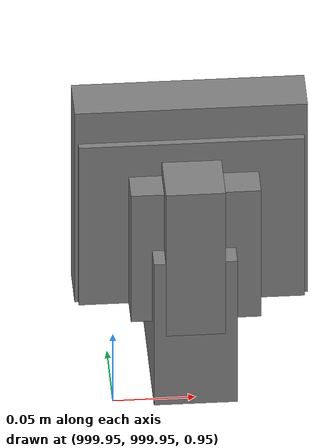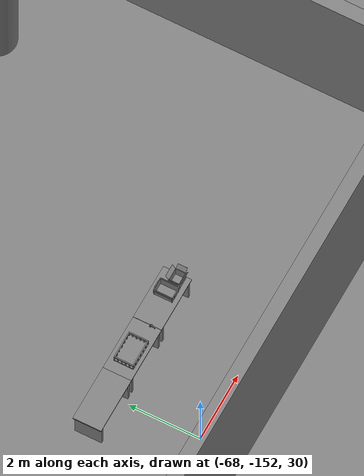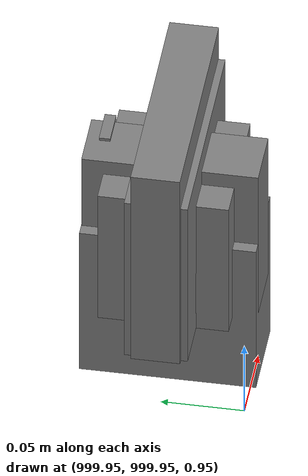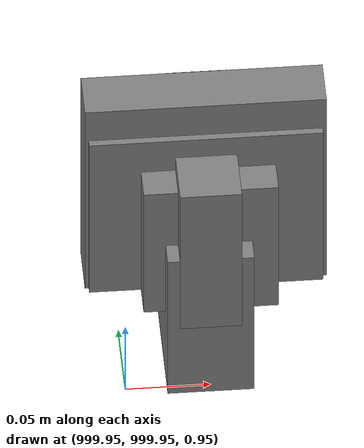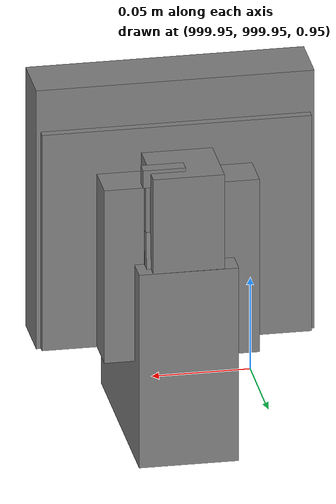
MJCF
<mujoco>
    <option gravity="0.000000000 0.000000000 -9.810000420" timestep="0.0049999999" integrator="implicitfast" density="1.225" viscosity="1.8000001e-05" noslip_iterations="10" iterations="100" sdf_iterations="50">
        <flag multiccd="disable"/>
    </option>
    <size memory="1000M"/>
    <compiler coordinate="local"/>
    <worldbody>
        <light cutoff="30" pos="0 1 1" dir="0 -1 -2"/>
        <light cutoff="30" pos="0 -1 1" dir="0 1 -2"/>
        <body pos="1000.000000000 1000.000000000 1.000000000" euler="0.000000000 0.000000000 180.000000000" name="openloong_gripper_2f85_fix_base_usda_wifi_box">
            <geom contype="1" conaffinity="1" density="1000" type="box" material="" rgba="0.500000000 0.500000000 0.500000000 1.000000000" solimp="0.899999976 0.949999988 0.001000000" friction="1.000000000 0.005000000 0.000100000" solref="0.020000000 1.000000000" margin="0" condim="3" group="0" pos="0.000000000 0.000000000 0.058978677" quat="0.000000000 0.000000047 0.000000000 1.000000000" size="0.068499997 0.018999999 0.059000000" name="openloong_gripper_2f85_fix_base_usda_geom_C4D19EBF_96A4_4DBD_AC7B_C71C9FCD2034"/>
            <freejoint name="openloong_gripper_2f85_fix_base_usda_wifi_box_joint"/>
            <site size="0.005000000 0.005000000 0.005000000" rgba="0.500000000 0.500000000 0.500000000 1.000000000" pos="0.000000000 0.000000000 0.000000000" quat="0.999961913 0.008726500 0.000000000 0.000000000" group="0" type="sphere" name="openloong_gripper_2f85_fix_base_usda_wifi_boxsite"/>
        </body>
        <body pos="-66.098197937 -149.093109131 31.164121628" euler="134.529998779 71.820625305 50.865543365" mocap="true" name="spotlight6_SpotLight"/>
        <body pos="1000.000000000 1000.000000000 1.000000000" euler="0.000011953 0.000005123 -179.999984741" name="openloong_gripper_2f85_fix_base_usda_intel_box">
            <geom contype="1" conaffinity="1" density="1000" type="box" material="" rgba="0.500000000 0.500000000 0.500000000 1.000000000" solimp="0.899999976 0.949999988 0.001000000" friction="1.000000000 0.005000000 0.000100000" solref="0.020000000 1.000000000" margin="0" condim="3" group="0" pos="0.000000000 -0.000067139 0.000082284" quat="0.707106709 0.000000225 0.000000253 0.707106650" size="0.052800003 0.025300000 0.052800003" name="openloong_gripper_2f85_fix_base_usda_geom_D2429BCF_854D_43EE_8C71_CC3ED261DB0C"/>
            <freejoint name="openloong_gripper_2f85_fix_base_usda_intel_box_joint"/>
            <site size="0.005000000 0.005000000 0.005000000" rgba="0.500000000 0.500000000 0.500000000 1.000000000" pos="0.000000000 0.000000000 0.000000000" quat="0.999961913 0.008726500 0.000000000 0.000000000" group="0" type="sphere" name="openloong_gripper_2f85_fix_base_usda_intel_boxsite"/>
        </body>
        <body pos="1000.000000000 999.999938965 1.000000000" euler="0.000000000 0.000000000 180.000000000" name="openloong_gripper_2f85_fix_base_usda_intelcore_i5">
            <geom contype="1" conaffinity="1" density="1000" type="box" material="" rgba="0.500000000 0.500000000 0.500000000 1.000000000" solimp="0.899999976 0.949999988 0.001000000" friction="1.000000000 0.005000000 0.000100000" solref="0.020000000 1.000000000" margin="0" condim="3" group="0" pos="0.000000000 0.000000000 0.051722717" quat="0.707106709 0.000000000 0.000000000 -0.707106769" size="0.052800000 0.018080002 0.052800000" name="openloong_gripper_2f85_fix_base_usda_geom_4CCCE4D3_E9DE_44F3_BE47_77B5B92B3F70"/>
            <freejoint name="openloong_gripper_2f85_fix_base_usda_intelcore_i5_joint"/>
            <site size="0.005000000 0.005000000 0.005000000" rgba="0.500000000 0.500000000 0.500000000 1.000000000" pos="0.000000000 0.000000000 0.000000000" quat="0.999961913 0.008726534 0.000000000 0.000000000" group="0" type="sphere" name="openloong_gripper_2f85_fix_base_usda_intelcore_i5site"/>
        </body>
        <body pos="-66.339294434 -149.296066284 31.163238525" euler="150.701797485 23.282415390 -176.974914551" mocap="true" name="spotlight2_SpotLight"/>
        <body pos="1000.000000000 1000.000000000 1.000000000" euler="0.000000000 0.000000000 180.000000000" name="openloong_gripper_2f85_fix_base_usda_cpu_fan">
            <geom contype="1" conaffinity="1" density="1000" type="box" material="" rgba="0.500000000 0.500000000 0.500000000 1.000000000" solimp="0.899999976 0.949999988 0.001000000" friction="1.000000000 0.005000000 0.000100000" solref="0.020000000 1.000000000" margin="0" condim="3" group="0" pos="0.000000000 0.000000000 0.070034981" quat="0.000000000 0.000000000 0.000000000 1.000000000" size="0.070700005 0.014699999 0.070700005" name="openloong_gripper_2f85_fix_base_usda_geom_790DE3D9_4427_4105_9DE2_99A8293D5816"/>
            <freejoint name="openloong_gripper_2f85_fix_base_usda_cpu_fan_joint"/>
            <site size="0.005000000 0.005000000 0.005000000" rgba="0.500000000 0.500000000 0.500000000 1.000000000" pos="0.000000000 0.000000000 0.000000000" quat="0.999961913 0.008726535 0.000000000 0.000000000" group="0" type="sphere" name="openloong_gripper_2f85_fix_base_usda_cpu_fancsite"/>
        </body>
        <body pos="-66.042465210 -149.715011597 31.170770645" euler="150.051681519 79.959899902 129.140640259" mocap="true" name="spotlight5_SpotLight"/>
        <body pos="1000.000000000 1000.000000000 1.000000000" euler="0.000000000 0.000000000 180.000000000" name="openloong_gripper_2f85_fix_base_usda_battery_01">
            <geom contype="1" conaffinity="1" density="1000" type="box" material="" rgba="0.500000000 0.500000000 0.500000000 1.000000000" solimp="0.899999976 0.949999988 0.001000000" friction="1.000000000 0.005000000 0.000100000" solref="0.020000000 1.000000000" margin="0" condim="3" group="0" pos="-0.011123657 -0.041940309 0.101691343" quat="1.000000000 0.000000000 0.000000000 0.000000000" size="0.010800000 0.003375000 0.004725000" name="openloong_gripper_2f85_fix_base_usda_geom_A7D590AA_E1D2_4EB5_A6F5_1C2613210E01"/>
            <geom contype="1" conaffinity="1" density="1000" type="box" material="" rgba="0.500000000 0.500000000 0.500000000 1.000000000" solimp="0.899999976 0.949999988 0.001000000" friction="1.000000000 0.005000000 0.000100000" solref="0.020000000 1.000000000" margin="0" condim="3" group="0" pos="-0.010876465 -0.044247437 0.047066893" quat="0.998702705 -0.050920475 0.000000000 0.000000000" size="0.009450001 0.002700000 0.024975000" name="openloong_gripper_2f85_fix_base_usda_geom_D0036F5B_106B_4DA9_B8AA_2D22A6F2C9EE"/>
            <geom contype="1" conaffinity="1" density="1000" type="box" material="" rgba="0.500000000 0.500000000 0.500000000 1.000000000" solimp="0.899999976 0.949999988 0.001000000" friction="1.000000000 0.005000000 0.000100000" solref="0.020000000 1.000000000" margin="0" condim="3" group="0" pos="-0.001235962 -0.000659180 0.047381196" quat="1.000000000 0.000000000 0.000000000 0.000000000" size="0.039420001 0.039150000 0.047250003" name="openloong_gripper_2f85_fix_base_usda_geom_A1EF7613_8F1C_479B_8BFE_346DBD2BB548"/>
            <geom contype="1" conaffinity="1" density="1000" type="box" material="" rgba="0.500000000 0.500000000 0.500000000 1.000000000" solimp="0.899999976 0.949999988 0.001000000" friction="1.000000000 0.005000000 0.000100000" solref="0.020000000 1.000000000" margin="0" condim="3" group="0" pos="-0.010876465 -0.039138794 0.009851727" quat="1.000000000 0.000000000 0.000000000 0.000000000" size="0.009450001 0.010800000 0.013500000" name="openloong_gripper_2f85_fix_base_usda_geom_8522142B_AE4D_4540_8D7A_79083B4F108C"/>
            <geom contype="1" conaffinity="1" density="1000" type="box" material="" rgba="0.500000000 0.500000000 0.500000000 1.000000000" solimp="0.899999976 0.949999988 0.001000000" friction="1.000000000 0.005000000 0.000100000" solref="0.020000000 1.000000000" margin="0" condim="3" group="0" pos="-0.010876465 -0.041528322 0.071508206" quat="1.000000000 0.000000000 0.000000000 0.000000000" size="0.009450001 0.002700000 0.027000001" name="openloong_gripper_2f85_fix_base_usda_geom_8FC2700E_5834_4D06_93A2_B08B4953AC37"/>
            <freejoint name="openloong_gripper_2f85_fix_base_usda_battery_01_joint"/>
            <site size="0.005000000 0.005000000 0.005000000" rgba="0.500000000 0.500000000 0.500000000 1.000000000" pos="0.000000000 0.000000000 0.000000000" quat="0.999961913 0.008726500 0.000000000 0.000000000" group="0" type="sphere" name="openloong_gripper_2f85_fix_base_usda_battery_01site"/>
        </body>
        <body pos="-64.866622925 -149.383972168 30.183746338" euler="89.999984741 89.999946594 0.000000000" name="openloong_gripper_2f85_fix_base_usda_bluebox_01">
            <geom contype="1" conaffinity="1" density="1000" type="box" material="" rgba="0.500000000 0.500000000 0.500000000 1.000000000" solimp="0.899999976 0.949999988 0.001000000" friction="1.000000000 0.005000000 0.000100000" solref="0.020000000 1.000000000" margin="0" condim="3" group="0" pos="0.276580811 0.187225342 0.000068665" quat="0.707106948 0.000077471 0.707106352 0.000077486" size="0.100000001 0.057999998 0.010000000" name="openloong_gripper_2f85_fix_base_usda_geom_1C5230F0_21CA_4A13_9C42_515667CF6EEE"/>
            <geom contype="1" conaffinity="1" density="1000" type="box" material="" rgba="0.500000000 0.500000000 0.500000000 1.000000000" solimp="0.899999976 0.949999988 0.001000000" friction="1.000000000 0.005000000 0.000100000" solref="0.020000000 1.000000000" margin="0" condim="3" group="0" pos="0.000000000 0.002883911 0.000000000" quat="0.999999881 0.000000000 0.000000000 0.000000000" size="0.254000008 0.003000000 0.172000006" name="openloong_gripper_2f85_fix_base_usda_geom_381C1CAF_F251_4084_9A37_0FA0DA8B42CE"/>
            <geom contype="1" conaffinity="1" density="1000" type="box" material="" rgba="0.500000000 0.500000000 0.500000000 1.000000000" solimp="0.899999976 0.949999988 0.001000000" friction="1.000000000 0.005000000 0.000100000" solref="0.020000000 1.000000000" margin="0" condim="3" group="0" pos="0.000000000 0.124874115 0.173484802" quat="0.999796331 0.020176515 -0.000000015 0.000000030" size="0.259999990 0.119999997 0.007000000" name="openloong_gripper_2f85_fix_base_usda_geom_1BA727AC_1EB6_4688_9240_79F574A80FB5"/>
            <geom contype="1" conaffinity="1" density="1000" type="box" material="" rgba="0.500000000 0.500000000 0.500000000 1.000000000" solimp="0.899999976 0.949999988 0.001000000" friction="1.000000000 0.005000000 0.000100000" solref="0.020000000 1.000000000" margin="0" condim="3" group="0" pos="0.000000000 0.124874115 -0.173469543" quat="0.999796331 -0.020176545 -0.000000015 0.000000000" size="0.259999990 0.119999997 0.007000000" name="openloong_gripper_2f85_fix_base_usda_geom_B6A7CD41_61AB_4748_81C2_F7D46E936FE8"/>
            <geom contype="1" conaffinity="1" density="1000" type="box" material="" rgba="0.500000000 0.500000000 0.500000000 1.000000000" solimp="0.899999976 0.949999988 0.001000000" friction="1.000000000 0.005000000 0.000100000" solref="0.020000000 1.000000000" margin="0" condim="3" group="0" pos="0.000000000 0.214008331 0.188980103" quat="0.999912977 0.013176724 0.000000015 0.000000000" size="0.259999990 0.029999999 0.012500000" name="openloong_gripper_2f85_fix_base_usda_geom_7CA0D81A_D2A4_4703_B0D3_1B8EA02B38C7"/>
            <geom contype="1" conaffinity="1" density="1000" type="box" material="" rgba="0.500000000 0.500000000 0.500000000 1.000000000" solimp="0.899999976 0.949999988 0.001000000" friction="1.000000000 0.005000000 0.000100000" solref="0.020000000 1.000000000" margin="0" condim="3" group="0" pos="-0.258361816 0.125289917 0.001876831" quat="0.702796936 -0.020792112 0.710783124 0.020769298" size="0.189999998 0.119999997 0.009000000" name="openloong_gripper_2f85_fix_base_usda_geom_2EEB5E86_490C_4690_B7B2_71A2649429E7"/>
            <geom contype="1" conaffinity="1" density="1000" type="box" material="" rgba="0.500000000 0.500000000 0.500000000 1.000000000" solimp="0.899999976 0.949999988 0.001000000" friction="1.000000000 0.005000000 0.000100000" solref="0.020000000 1.000000000" margin="0" condim="3" group="0" pos="0.000000000 0.214008331 -0.188980103" quat="0.999912977 -0.013176769 0.000000030 0.000000015" size="0.259999990 0.029999999 0.012500000" name="openloong_gripper_2f85_fix_base_usda_geom_F1F63D3A_CACC_480B_BD0F_51D4E6B9B78E"/>
            <geom contype="1" conaffinity="1" density="1000" type="box" material="" rgba="0.500000000 0.500000000 0.500000000 1.000000000" solimp="0.899999976 0.949999988 0.001000000" friction="1.000000000 0.005000000 0.000100000" solref="0.020000000 1.000000000" margin="0" condim="3" group="0" pos="-0.276611328 0.187225342 0.000068665" quat="0.707106650 0.000077441 0.707106709 0.000077456" size="0.100000001 0.057999998 0.010000000" name="openloong_gripper_2f85_fix_base_usda_geom_DA360A4A_0DE3_47C7_B5ED_F3CA2BC94F2D"/>
            <geom contype="1" conaffinity="1" density="1000" type="box" material="" rgba="0.500000000 0.500000000 0.500000000 1.000000000" solimp="0.899999976 0.949999988 0.001000000" friction="1.000000000 0.005000000 0.000100000" solref="0.020000000 1.000000000" margin="0" condim="3" group="0" pos="0.258331299 0.125289917 0.001876831" quat="0.702851415 0.018856421 0.710823774 -0.019329369" size="0.189999998 0.119999997 0.009000000" name="openloong_gripper_2f85_fix_base_usda_geom_1924B67C_D12C_47F3_BD26_C04B1D28B406"/>
            <freejoint name="openloong_gripper_2f85_fix_base_usda_bluebox_01_joint"/>
            <site size="0.005000000 0.005000000 0.005000000" rgba="0.500000000 0.500000000 0.500000000 1.000000000" pos="0.000000000 0.000000000 0.000000000" quat="0.999961913 0.008726534 0.000000000 0.000000000" group="0" type="sphere" name="openloong_gripper_2f85_fix_base_usda_bluebox_01site"/>
        </body>
        <body pos="-64.496299744 -149.491867065 30.235729218" euler="0.000000000 0.000000000 89.999946594" name="openloong_gripper_2f85_fix_base_usda_cardboardbox_01">
            <geom contype="1" conaffinity="1" density="1000" type="box" material="" rgba="0.500000000 0.500000000 0.500000000 1.000000000" solimp="0.899999976 0.949999988 0.001000000" friction="1.000000000 0.005000000 0.000100000" solref="0.020000000 1.000000000" margin="0" condim="3" group="0" pos="-0.003166199 -0.004086494 0.005052090" quat="1.000000000 0.000000000 0.000000000 0.000000000" size="0.142499998 0.177500010 0.005000000" name="openloong_gripper_2f85_fix_base_usda_geom_D2469A9B_AFF3_4EE3_8124_DBF78C806B99"/>
            <geom contype="1" conaffinity="1" density="1000" type="box" material="" rgba="0.500000000 0.500000000 0.500000000 1.000000000" solimp="0.899999976 0.949999988 0.001000000" friction="1.000000000 0.005000000 0.000100000" solref="0.020000000 1.000000000" margin="0" condim="3" group="0" pos="-0.003166199 0.170316696 0.150570869" quat="1.000000000 0.000000000 0.000000000 0.000000000" size="0.142499998 0.005000000 0.149999991" name="openloong_gripper_2f85_fix_base_usda_geom_05F71F8B_6DC7_4C3C_8EFA_718591B40E57"/>
            <geom contype="1" conaffinity="1" density="1000" type="box" material="" rgba="0.500000000 0.500000000 0.500000000 1.000000000" solimp="0.899999976 0.949999988 0.001000000" friction="1.000000000 0.005000000 0.000100000" solref="0.020000000 1.000000000" margin="0" condim="3" group="0" pos="-0.147399902 -0.005307198 0.150570869" quat="1.000000000 0.000000000 0.000000000 0.000000000" size="0.005000000 0.177500010 0.149999991" name="openloong_gripper_2f85_fix_base_usda_geom_CBD4A4DE_8CAC_4F6B_A8B5_D1B16BB0CC22"/>
            <geom contype="1" conaffinity="1" density="1000" type="box" material="" rgba="0.500000000 0.500000000 0.500000000 1.000000000" solimp="0.899999976 0.949999988 0.001000000" friction="1.000000000 0.005000000 0.000100000" solref="0.020000000 1.000000000" margin="0" condim="3" group="0" pos="0.140275955 -0.005307198 0.150570869" quat="1.000000000 0.000000000 0.000000000 0.000000000" size="0.005000000 0.177500010 0.149999991" name="openloong_gripper_2f85_fix_base_usda_geom_E5A53BC9_2278_42E0_8CB0_390AF9975691"/>
            <geom contype="1" conaffinity="1" density="1000" type="box" material="" rgba="0.500000000 0.500000000 0.500000000 1.000000000" solimp="0.899999976 0.949999988 0.001000000" friction="1.000000000 0.005000000 0.000100000" solref="0.020000000 1.000000000" margin="0" condim="3" group="0" pos="-0.003166199 -0.181550980 0.150570869" quat="1.000000000 0.000000000 0.000000000 0.000000000" size="0.142499998 0.005000000 0.149999991" name="openloong_gripper_2f85_fix_base_usda_geom_6133E258_25A3_4C85_A5AA_36876785CA5A"/>
            <freejoint name="openloong_gripper_2f85_fix_base_usda_cardboardbox_01_joint"/>
            <site size="0.005000000 0.005000000 0.005000000" rgba="0.500000000 0.500000000 0.500000000 1.000000000" pos="0.000000000 0.000000000 0.000000000" quat="0.999961913 0.008726535 0.000000000 0.000000000" group="0" type="sphere" name="openloong_gripper_2f85_fix_base_usda_site_8A2102C9_C5EB_4C7F_B523_7A4F94EA832F"/>
            <body pos="0.139160156 -0.004048347 0.301930904" euler="-179.999954224 49.383502960 179.999954224" name="openloong_gripper_2f85_fix_base_usda_A1_006">
                <geom contype="1" conaffinity="1" density="1000" type="box" material="" rgba="0.500000000 0.500000000 0.500000000 1.000000000" solimp="0.899999976 0.949999988 0.001000000" friction="1.000000000 0.005000000 0.000100000" solref="0.020000000 1.000000000" margin="0" condim="3" group="0" pos="-0.071587563 0.000009537 0.001745224" quat="0.999999881 0.000000000 0.000000000 0.000000000" size="0.071249999 0.179999992 0.002500000" name="openloong_gripper_2f85_fix_base_usda_geom_D4276FCE_F924_413A_B9E7_0FD17F14A03E"/>
                <joint armature="0" stiffness="0.07" damping="0.0099999998" axis="0.000000 1.000000 0.000000" type="hinge" name="openloong_gripper_2f85_fix_base_usda_A1_006"/>
            </body>
            <body pos="-0.145902634 -0.004086494 0.301938057" euler="-180.000000000 -60.000011444 -180.000000000" name="openloong_gripper_2f85_fix_base_usda_A2_006">
                <geom contype="1" conaffinity="1" density="1000" type="box" material="" rgba="0.500000000 0.500000000 0.500000000 1.000000000" solimp="0.899999976 0.949999988 0.001000000" friction="1.000000000 0.005000000 0.000100000" solref="0.020000000 1.000000000" margin="0" condim="3" group="0" pos="0.071268082 0.000009537 0.002717972" quat="0.000002921 0.000000000 -0.000000030 0.999999881" size="0.071249999 0.179999992 0.002500000" name="openloong_gripper_2f85_fix_base_usda_geom_C9EE3FAE_F46A_4E8E_85B5_FB629E3F987F"/>
                <joint armature="0" stiffness="0.07" damping="0.0099999998" axis="0.000000 1.000000 0.000000" type="hinge" name="openloong_gripper_2f85_fix_base_usda_A2_006"/>
            </body>
            <body pos="-0.003385544 0.175991058 0.301930904" euler="-125.858116150 -0.000004561 0.000002331" name="openloong_gripper_2f85_fix_base_usda_B2_006">
                <geom contype="1" conaffinity="1" density="1000" type="box" material="" rgba="0.500000000 0.500000000 0.500000000 1.000000000" solimp="0.899999976 0.949999988 0.001000000" friction="1.000000000 0.005000000 0.000100000" solref="0.020000000 1.000000000" margin="0" condim="3" group="0" pos="0.000009537 -0.070939064 -0.002470016" quat="0.999614120 0.027776197 -0.000000015 0.000000030" size="0.137500003 0.064999998 0.005000000" name="openloong_gripper_2f85_fix_base_usda_geom_94D85BC7_6652_4C67_BAB4_C0AC5EF08009"/>
                <joint armature="0" stiffness="0.07" damping="0.0099999998" axis="1.000000 0.000000 0.000000" type="hinge" name="openloong_gripper_2f85_fix_base_usda_B2_006"/>
            </body>
            <body pos="-0.003385544 -0.184140205 0.301938057" euler="147.805557251 0.000000000 0.000000000" name="openloong_gripper_2f85_fix_base_usda_B1_006">
                <geom contype="1" conaffinity="1" density="1000" type="box" material="" rgba="0.500000000 0.500000000 0.500000000 1.000000000" solimp="0.899999976 0.949999988 0.001000000" friction="1.000000000 0.005000000 0.000100000" solref="0.020000000 1.000000000" margin="0" condim="3" group="0" pos="-0.000028610 0.070202351 -0.002703667" quat="0.999614179 -0.027776167 0.000000000 0.000000000" size="0.137500003 0.064999998 0.005000000" name="openloong_gripper_2f85_fix_base_usda_geom_8D5626EA_7D1E_49CB_8A33_A293AA67E349"/>
                <joint armature="0" stiffness="0.07" damping="0.0099999998" axis="1.000000 0.000000 0.000000" type="hinge" name="openloong_gripper_2f85_fix_base_usda_B1_006"/>
            </body>
        </body>
        <body pos="-65.882858276 -149.481979370 30.229999542" euler="-64.487716675 0.000000000 0.000000000" name="openloong_gripper_2f85_fix_base_usda_Barcode">
            <geom contype="1" conaffinity="1" density="1000" type="box" material="" rgba="0.500000000 0.500000000 0.500000000 1.000000000" solimp="0.899999976 0.949999988 0.001000000" friction="1.000000000 0.005000000 0.000100000" solref="0.020000000 1.000000000" margin="0" condim="3" group="0" pos="0.000000000 0.013038635 0.001419067" quat="0.000000000 0.000000000 0.000000000 1.000000119" size="0.034000002 0.010000000 0.017999999" name="openloong_gripper_2f85_fix_base_usda_geom_2F144DE4_745C_4E91_BAA5_E8968E20A372"/>
            <geom contype="1" conaffinity="1" density="1000" type="box" material="" rgba="0.500000000 0.500000000 0.500000000 1.000000000" solimp="0.899999976 0.949999988 0.001000000" friction="1.000000000 0.005000000 0.000100000" solref="0.020000000 1.000000000" margin="0" condim="3" group="0" pos="0.000000000 -0.035301208 -0.007095337" quat="0.000000000 0.000000000 -0.043619365 0.999048233" size="0.028999999 0.010000000 0.020000000" name="openloong_gripper_2f85_fix_base_usda_geom_68305178_3915_428D_8C05_8EB96FA43FEB"/>
            <geom contype="1" conaffinity="1" density="1000" type="box" material="" rgba="0.500000000 0.500000000 0.500000000 1.000000000" solimp="0.899999976 0.949999988 0.001000000" friction="1.000000000 0.005000000 0.000100000" solref="0.020000000 1.000000000" margin="0" condim="3" group="0" pos="0.000000000 -0.043411255 -0.011749268" quat="0.922262907 0.386563420 0.000000000 0.000000000" size="0.026000001 0.010000000 0.020000000" name="openloong_gripper_2f85_fix_base_usda_geom_5DCBDFBA_C9BC_4C55_967D_C9CBD498C091"/>
            <geom contype="1" conaffinity="1" density="1000" type="box" material="" rgba="0.500000000 0.500000000 0.500000000 1.000000000" solimp="0.899999976 0.949999988 0.001000000" friction="1.000000000 0.005000000 0.000100000" solref="0.020000000 1.000000000" margin="0" condim="3" group="0" pos="0.000000000 -0.016967773 -0.031860352" quat="0.000000000 0.000000000 0.000000000 1.000000119" size="0.008000000 0.010000000 0.013000000" name="openloong_gripper_2f85_fix_base_usda_geom_A38E2251_9F26_4724_B33E_4F6F1C6C7498"/>
            <geom contype="1" conaffinity="1" density="1000" type="box" material="" rgba="0.500000000 0.500000000 0.500000000 1.000000000" solimp="0.899999976 0.949999988 0.001000000" friction="1.000000000 0.005000000 0.000100000" solref="0.020000000 1.000000000" margin="0" condim="3" group="0" pos="0.000000000 -0.001869202 0.000312805" quat="0.953716993 0.300705761 0.000000000 0.000000000" size="0.032000002 0.010000000 0.018999999" name="openloong_gripper_2f85_fix_base_usda_geom_23397705_239B_45D8_B65C_C6FB5B40FB33"/>
            <geom contype="1" conaffinity="1" density="1000" type="box" material="" rgba="0.500000000 0.500000000 0.500000000 1.000000000" solimp="0.899999976 0.949999988 0.001000000" friction="1.000000000 0.005000000 0.000100000" solref="0.020000000 1.000000000" margin="0" condim="3" group="0" pos="0.000000000 -0.019531250 -0.003173828" quat="0.953716993 0.300705761 0.000000000 0.000000000" size="0.030999999 0.010000000 0.020000000" name="openloong_gripper_2f85_fix_base_usda_geom_45261BD2_64B3_409A_9A52_3B8D09E6966A"/>
            <geom contype="1" conaffinity="1" density="1000" type="box" material="" rgba="0.500000000 0.500000000 0.500000000 1.000000000" solimp="0.899999976 0.949999988 0.001000000" friction="1.000000000 0.005000000 0.000100000" solref="0.020000000 1.000000000" margin="0" condim="3" group="0" pos="0.000000000 -0.035301208 -0.007095337" quat="0.953716993 0.300705761 0.000000000 0.000000000" size="0.028999999 0.010000000 0.020000000" name="openloong_gripper_2f85_fix_base_usda_geom_97B061DC_B23F_4710_9200_51A32F14DF23"/>
            <geom contype="1" conaffinity="1" density="1000" type="box" material="" rgba="0.500000000 0.500000000 0.500000000 1.000000000" solimp="0.899999976 0.949999988 0.001000000" friction="1.000000000 0.005000000 0.000100000" solref="0.020000000 1.000000000" margin="0" condim="3" group="0" pos="0.000000000 -0.042617798 -0.071121216" quat="0.000000000 0.000000000 0.000000000 1.000000119" size="0.013000000 0.021000000 0.059999999" name="openloong_gripper_2f85_fix_base_usda_geom_214FA3BB_6E08_492E_A0F8_2B8FFC8B886E"/>
            <freejoint name="openloong_gripper_2f85_fix_base_usda_Barcode_joint"/>
            <site size="0.005000000 0.005000000 0.005000000" rgba="0.500000000 0.500000000 0.500000000 1.000000000" pos="0.000000000 0.000000000 0.000000000" quat="1.000000000 0.000000000 0.000000000 0.000000000" group="0" type="sphere" name="openloong_gripper_2f85_fix_base_usda_Barcode_site"/>
        </body>
        <body pos="-66.745018005 -149.392349243 30.184000015" euler="0.000000000 0.000000000 89.999946594" name="[22330518012155]_Basket_01">
            <geom contype="1" conaffinity="1" density="1000" type="box" material="" rgba="0.500000000 0.500000000 0.500000000 1.000000000" solimp="0.899999976 0.949999988 0.001000000" friction="1.000000000 0.005000000 0.000100000" solref="0.020000000 1.000000000" margin="0" condim="3" group="0" pos="-0.052425385 0.389207840 0.089787483" quat="0.707107008 0.000000000 0.000000000 0.707106411" size="0.014249999 0.014249999 0.059999999" name="[22330518012155]_geom_18FC5D73_FF54_4B43_80B3_0627410B32DA"/>
            <geom contype="1" conaffinity="1" density="1000" type="box" material="" rgba="0.500000000 0.500000000 0.500000000 1.000000000" solimp="0.899999976 0.949999988 0.001000000" friction="1.000000000 0.005000000 0.000100000" solref="0.020000000 1.000000000" margin="0" condim="3" group="0" pos="0.264015198 -0.133043289 0.089787483" quat="0.707107008 0.000000000 0.000000000 0.707106411" size="0.014249999 0.014249999 0.059999999" name="[22330518012155]_geom_EA6ECEE7_9D98_4B6D_AD56_4B469C507698"/>
            <geom contype="1" conaffinity="1" density="1000" type="box" material="" rgba="0.500000000 0.500000000 0.500000000 1.000000000" solimp="0.899999976 0.949999988 0.001000000" friction="1.000000000 0.005000000 0.000100000" solref="0.020000000 1.000000000" margin="0" condim="3" group="0" pos="-0.264015198 -0.265548706 0.089793205" quat="0.707107008 0.000000000 0.000000000 0.707106411" size="0.014249999 0.014249999 0.059999999" name="[22330518012155]_geom_A6C6CE12_BA5D_49D7_BBBB_95B3CA3C7C00"/>
            <geom contype="1" conaffinity="1" density="1000" type="box" material="" rgba="0.500000000 0.500000000 0.500000000 1.000000000" solimp="0.899999976 0.949999988 0.001000000" friction="1.000000000 0.005000000 0.000100000" solref="0.020000000 1.000000000" margin="0" condim="3" group="0" pos="-0.160263062 -0.389322281 0.089793205" quat="0.707107008 0.000000000 0.000000000 0.707106411" size="0.014249999 0.014249999 0.059999999" name="[22330518012155]_geom_A07E3E6F_1F9A_4764_A603_51101A6841E3"/>
            <geom contype="1" conaffinity="1" density="1000" type="box" material="" rgba="0.500000000 0.500000000 0.500000000 1.000000000" solimp="0.899999976 0.949999988 0.001000000" friction="1.000000000 0.005000000 0.000100000" solref="0.020000000 1.000000000" margin="0" condim="3" group="0" pos="0.162265778 -0.389322281 0.089787483" quat="0.707107008 0.000000000 0.000000000 0.707106411" size="0.014249999 0.014249999 0.059999999" name="[22330518012155]_geom_1F80827E_FA27_4FE5_B99A_C432F4A10F4A"/>
            <geom contype="1" conaffinity="1" density="1000" type="box" material="" rgba="0.500000000 0.500000000 0.500000000 1.000000000" solimp="0.899999976 0.949999988 0.001000000" friction="1.000000000 0.005000000 0.000100000" solref="0.020000000 1.000000000" margin="0" condim="3" group="0" pos="0.264015198 0.389207840 0.089787483" quat="0.707107008 0.000000000 0.000000000 0.707106411" size="0.014249999 0.014249999 0.059999999" name="[22330518012155]_geom_F9B925F5_8FC2_4BED_8E4D_15C4760801D4"/>
            <geom contype="1" conaffinity="1" density="1000" type="box" material="" rgba="0.500000000 0.500000000 0.500000000 1.000000000" solimp="0.899999976 0.949999988 0.001000000" friction="1.000000000 0.005000000 0.000100000" solref="0.020000000 1.000000000" margin="0" condim="3" group="0" pos="-0.264015198 -0.133043289 0.089793205" quat="0.707107008 0.000000000 0.000000000 0.707106411" size="0.014249999 0.014249999 0.059999999" name="[22330518012155]_geom_45585005_ED93_465A_8AC4_566C82B744D0"/>
            <geom contype="1" conaffinity="1" density="1000" type="box" material="" rgba="0.500000000 0.500000000 0.500000000 1.000000000" solimp="0.899999976 0.949999988 0.001000000" friction="1.000000000 0.005000000 0.000100000" solref="0.020000000 1.000000000" margin="0" condim="3" group="0" pos="-0.264026642 0.269256592 0.089793205" quat="0.707107008 0.000000000 0.000000000 0.707106411" size="0.014249999 0.014249999 0.059999999" name="[22330518012155]_geom_4EF25414_B91A_4B39_88ED_E30730401C2B"/>
            <geom contype="1" conaffinity="1" density="1000" type="box" material="" rgba="0.500000000 0.500000000 0.500000000 1.000000000" solimp="0.899999976 0.949999988 0.001000000" friction="1.000000000 0.005000000 0.000100000" solref="0.020000000 1.000000000" margin="0" condim="3" group="0" pos="0.054462433 0.389207840 0.089787483" quat="0.707107008 0.000000000 0.000000000 0.707106411" size="0.014249999 0.014249999 0.059999999" name="[22330518012155]_geom_814A098B_38BD_45C7_BE89_B519FB154EFA"/>
            <geom contype="1" conaffinity="1" density="1000" type="box" material="" rgba="0.500000000 0.500000000 0.500000000 1.000000000" solimp="0.899999976 0.949999988 0.001000000" friction="1.000000000 0.005000000 0.000100000" solref="0.020000000 1.000000000" margin="0" condim="3" group="0" pos="0.054462433 -0.389322281 0.089787483" quat="0.707107008 0.000000000 0.000000000 0.707106411" size="0.014249999 0.014249999 0.059999999" name="[22330518012155]_geom_8E8067C4_47B4_465F_A527_52378B65DB50"/>
            <geom contype="1" conaffinity="1" density="1000" type="box" material="" rgba="0.500000000 0.500000000 0.500000000 1.000000000" solimp="0.899999976 0.949999988 0.001000000" friction="1.000000000 0.005000000 0.000100000" solref="0.020000000 1.000000000" margin="0" condim="3" group="0" pos="0.264015198 0.269256592 0.089793205" quat="0.707107008 0.000000000 0.000000000 0.707106411" size="0.014249999 0.014249999 0.059999999" name="[22330518012155]_geom_EB24C1B4_66DF_4834_8913_DFC25AEE2AFA"/>
            <geom contype="1" conaffinity="1" density="1000" type="box" material="" rgba="0.500000000 0.500000000 0.500000000 1.000000000" solimp="0.899999976 0.949999988 0.001000000" friction="1.000000000 0.005000000 0.000100000" solref="0.020000000 1.000000000" margin="0" condim="3" group="0" pos="0.264015198 -0.389322281 0.089787483" quat="0.707107008 0.000000000 0.000000000 0.707106411" size="0.014249999 0.014249999 0.059999999" name="[22330518012155]_geom_6BAE60E2_33B1_4584_A578_8E02F705CDC3"/>
            <geom contype="1" conaffinity="1" density="1000" type="box" material="" rgba="0.500000000 0.500000000 0.500000000 1.000000000" solimp="0.899999976 0.949999988 0.001000000" friction="1.000000000 0.005000000 0.000100000" solref="0.020000000 1.000000000" margin="0" condim="3" group="0" pos="0.000000000 0.000000000 0.015998840" quat="0.707107008 0.000000000 0.000000000 0.707106411" size="0.403499991 0.279000014 0.015750000" name="[22330518012155]_geom_B3AF45B4_1233_408C_9773_F052E4C51ABB"/>
            <geom contype="1" conaffinity="1" density="1000" type="box" material="" rgba="0.500000000 0.500000000 0.500000000 1.000000000" solimp="0.899999976 0.949999988 0.001000000" friction="1.000000000 0.005000000 0.000100000" solref="0.020000000 1.000000000" margin="0" condim="3" group="0" pos="0.000000000 -0.389476776 0.163619041" quat="0.707107008 0.000000000 0.000000000 0.707106411" size="0.015000000 0.277500004 0.015750000" name="[22330518012155]_geom_D434B50E_053B_40B9_81EE_F0D7EF2A9982"/>
            <geom contype="1" conaffinity="1" density="1000" type="box" material="" rgba="0.500000000 0.500000000 0.500000000 1.000000000" solimp="0.899999976 0.949999988 0.001000000" friction="1.000000000 0.005000000 0.000100000" solref="0.020000000 1.000000000" margin="0" condim="3" group="0" pos="0.162265778 0.389207840 0.089787483" quat="0.707107008 0.000000000 0.000000000 0.707106411" size="0.014249999 0.014249999 0.059999999" name="[22330518012155]_geom_E383CD55_D04B_4C08_9861_A16DCF4FA93E"/>
            <geom contype="1" conaffinity="1" density="1000" type="box" material="" rgba="0.500000000 0.500000000 0.500000000 1.000000000" solimp="0.899999976 0.949999988 0.001000000" friction="1.000000000 0.005000000 0.000100000" solref="0.020000000 1.000000000" margin="0" condim="3" group="0" pos="0.000000000 0.389471054 0.163619041" quat="0.707107008 0.000000000 0.000000000 0.707106411" size="0.015000000 0.277500004 0.015750000" name="[22330518012155]_geom_407C8567_1889_43FF_B4A8_D7BFA4D771A3"/>
            <geom contype="1" conaffinity="1" density="1000" type="box" material="" rgba="0.500000000 0.500000000 0.500000000 1.000000000" solimp="0.899999976 0.949999988 0.001000000" friction="1.000000000 0.005000000 0.000100000" solref="0.020000000 1.000000000" margin="0" condim="3" group="0" pos="-0.263511658 0.000000000 0.163619041" quat="0.707107008 0.000000000 0.000000000 0.707106411" size="0.403499991 0.015000000 0.015750000" name="[22330518012155]_geom_E668CB5C_0D4C_4451_9207_5FC5F147C84D"/>
            <geom contype="1" conaffinity="1" density="1000" type="box" material="" rgba="0.500000000 0.500000000 0.500000000 1.000000000" solimp="0.899999976 0.949999988 0.001000000" friction="1.000000000 0.005000000 0.000100000" solref="0.020000000 1.000000000" margin="0" condim="3" group="0" pos="-0.264015198 0.141334534 0.089793205" quat="0.707107008 0.000000000 0.000000000 0.707106411" size="0.014249999 0.014249999 0.059999999" name="[22330518012155]_geom_9BF6011D_D8CC_4DA3_8CC4_1C385DE3BCB2"/>
            <geom contype="1" conaffinity="1" density="1000" type="box" material="" rgba="0.500000000 0.500000000 0.500000000 1.000000000" solimp="0.899999976 0.949999988 0.001000000" friction="1.000000000 0.005000000 0.000100000" solref="0.020000000 1.000000000" margin="0" condim="3" group="0" pos="0.264015198 -0.265548706 0.089787483" quat="0.707107008 0.000000000 0.000000000 0.707106411" size="0.014249999 0.014249999 0.059999999" name="[22330518012155]_geom_94D0DB65_8268_4A2C_95A8_1FB142ED2DDF"/>
            <geom contype="1" conaffinity="1" density="1000" type="box" material="" rgba="0.500000000 0.500000000 0.500000000 1.000000000" solimp="0.899999976 0.949999988 0.001000000" friction="1.000000000 0.005000000 0.000100000" solref="0.020000000 1.000000000" margin="0" condim="3" group="0" pos="-0.160263062 0.389207840 0.089787483" quat="0.707107008 0.000000000 0.000000000 0.707106411" size="0.014249999 0.014249999 0.059999999" name="[22330518012155]_geom_780A4C23_3D22_4AA6_9A78_02BE117E4092"/>
            <geom contype="1" conaffinity="1" density="1000" type="box" material="" rgba="0.500000000 0.500000000 0.500000000 1.000000000" solimp="0.899999976 0.949999988 0.001000000" friction="1.000000000 0.005000000 0.000100000" solref="0.020000000 1.000000000" margin="0" condim="3" group="0" pos="-0.052425385 -0.389322281 0.089787483" quat="0.707107008 0.000000000 0.000000000 0.707106411" size="0.014249999 0.014249999 0.059999999" name="[22330518012155]_geom_3FC0EFDC_92F9_475D_BDC8_FB94585DE616"/>
            <geom contype="1" conaffinity="1" density="1000" type="box" material="" rgba="0.500000000 0.500000000 0.500000000 1.000000000" solimp="0.899999976 0.949999988 0.001000000" friction="1.000000000 0.005000000 0.000100000" solref="0.020000000 1.000000000" margin="0" condim="3" group="0" pos="-0.264026642 -0.389322281 0.089793205" quat="0.707107008 0.000000000 0.000000000 0.707106411" size="0.014249999 0.014249999 0.059999999" name="[22330518012155]_geom_CA62099A_64E5_4B4E_B152_612E0DEEEC62"/>
            <geom contype="1" conaffinity="1" density="1000" type="box" material="" rgba="0.500000000 0.500000000 0.500000000 1.000000000" solimp="0.899999976 0.949999988 0.001000000" friction="1.000000000 0.005000000 0.000100000" solref="0.020000000 1.000000000" margin="0" condim="3" group="0" pos="0.264015198 0.141334534 0.089787483" quat="0.707107008 0.000000000 0.000000000 0.707106411" size="0.014249999 0.014249999 0.059999999" name="[22330518012155]_geom_72E249D5_A2A2_41F1_A076_A58BEF2D02C2"/>
            <geom contype="1" conaffinity="1" density="1000" type="box" material="" rgba="0.500000000 0.500000000 0.500000000 1.000000000" solimp="0.899999976 0.949999988 0.001000000" friction="1.000000000 0.005000000 0.000100000" solref="0.020000000 1.000000000" margin="0" condim="3" group="0" pos="-0.264015198 0.389207840 0.089793205" quat="0.707107008 0.000000000 0.000000000 0.707106411" size="0.014249999 0.014249999 0.059999999" name="[22330518012155]_geom_C94A7EAE_CE32_49D5_9250_B1531BCF17A8"/>
            <geom contype="1" conaffinity="1" density="1000" type="box" material="" rgba="0.500000000 0.500000000 0.500000000 1.000000000" solimp="0.899999976 0.949999988 0.001000000" friction="1.000000000 0.005000000 0.000100000" solref="0.020000000 1.000000000" margin="0" condim="3" group="0" pos="0.264015198 0.004480362 0.089787483" quat="0.707107008 0.000000000 0.000000000 0.707106411" size="0.014249999 0.014249999 0.059999999" name="[22330518012155]_geom_567124E1_16AF_4021_B091_05B10B0B57FD"/>
            <geom contype="1" conaffinity="1" density="1000" type="box" material="" rgba="0.500000000 0.500000000 0.500000000 1.000000000" solimp="0.899999976 0.949999988 0.001000000" friction="1.000000000 0.005000000 0.000100000" solref="0.020000000 1.000000000" margin="0" condim="3" group="0" pos="0.263694763 -0.000011444 0.163619041" quat="0.707107008 0.000000000 0.000000000 0.707106411" size="0.403499991 0.015000000 0.015750000" name="[22330518012155]_geom_55FA9CF8_B2B2_4BD0_8FE7_514AC9A2CDD4"/>
            <geom contype="1" conaffinity="1" density="1000" type="box" material="" rgba="0.500000000 0.500000000 0.500000000 1.000000000" solimp="0.899999976 0.949999988 0.001000000" friction="1.000000000 0.005000000 0.000100000" solref="0.020000000 1.000000000" margin="0" condim="3" group="0" pos="-0.264015198 0.004480362 0.089793205" quat="0.707107008 0.000000000 0.000000000 0.707106411" size="0.014249999 0.014249999 0.059999999" name="[22330518012155]_geom_321A0070_5323_4475_B03B_84F10A5A27F9"/>
            <freejoint name="[22330518012155]_joint_E84428C6_9C2B_4596_BDA8_0EF61DAB052C"/>
        </body>
        <body pos="0.000000000 0.000000000 0.000000000" euler="0.000000000 0.000000000 0.000000000" name="Static Objects_Static Objects">
            <geom contype="1" conaffinity="1" density="1000" type="box" material="" rgba="0.500000000 0.500000000 0.500000000 1.000000000" solimp="0.899999976 0.949999988 0.001000000" friction="1.000000000 0.005000000 0.000100000" solref="0.020000000 1.000000000" margin="0" condim="3" group="0" pos="-67.544113159 -149.365814209 29.727830887" quat="0.500000417 0.499999970 0.499999553 0.499999970" size="0.381000012 0.319999993 0.041000001" name="Static Objects_geom_B63E597F_3FD5_4486_B0C0_ECD80ACA813C"/>
            <geom contype="1" conaffinity="1" density="1000" type="box" material="" rgba="0.500000000 0.500000000 0.500000000 1.000000000" solimp="0.899999976 0.949999988 0.001000000" friction="1.000000000 0.005000000 0.000100000" solref="0.020000000 1.000000000" margin="0" condim="3" group="0" pos="-68.239501953 -149.365814209 30.086868286" quat="0.500000417 0.499999970 0.499999553 0.499999970" size="0.370999992 0.039500002 0.745000005" name="Static Objects_geom_8DC0212E_DED9_410F_A505_87245950C3E1"/>
            <geom contype="1" conaffinity="1" density="1000" type="box" material="" rgba="0.500000000 0.500000000 0.500000000 1.000000000" solimp="0.899999976 0.949999988 0.001000000" friction="1.000000000 0.005000000 0.000100000" solref="0.020000000 1.000000000" margin="0" condim="3" group="0" pos="-68.239501953 -149.365814209 30.147235870" quat="0.500000417 0.499999970 0.499999553 0.499999970" size="0.400000006 0.022000000 0.800000012" name="Static Objects_geom_2DFC92BE_2095_49A4_A9C3_97548C20F515"/>
            <geom contype="1" conaffinity="1" density="1000" type="box" material="" rgba="0.500000000 0.500000000 0.500000000 1.000000000" solimp="0.899999976 0.949999988 0.001000000" friction="1.000000000 0.005000000 0.000100000" solref="0.020000000 1.000000000" margin="0" condim="3" group="0" pos="-68.934890747 -149.365814209 29.727830887" quat="0.500000417 0.499999970 0.499999553 0.499999970" size="0.381000012 0.319999993 0.041000001" name="Static Objects_geom_0D9B6BB7_1732_4E63_A999_0BA29BAE8607"/>
            <geom contype="1" conaffinity="1" density="1000" type="box" material="" rgba="0.500000000 0.500000000 0.500000000 1.000000000" solimp="0.899999976 0.949999988 0.001000000" friction="1.000000000 0.005000000 0.000100000" solref="0.020000000 1.000000000" margin="0" condim="3" group="0" pos="-68.239501953 -149.365814209 29.561563492" quat="0.500000417 0.499999970 0.499999553 0.499999970" size="0.020000000 0.022000000 0.660000026" name="Static Objects_geom_BC9B9662_0585_41D0_8DD8_70F3CFFE008B"/>
            <geom contype="1" conaffinity="1" density="1000" type="box" material="" rgba="0.500000000 0.500000000 0.500000000 1.000000000" solimp="0.899999976 0.949999988 0.001000000" friction="1.000000000 0.005000000 0.000100000" solref="0.020000000 1.000000000" margin="0" condim="3" group="0" pos="-65.945671082 -149.365814209 29.727830887" quat="0.500000417 0.499999970 0.499999553 0.499999970" size="0.381000012 0.319999993 0.041000001" name="Static Objects_geom_54BAAEE8_1A61_453E_9834_5E55B1D72FCD"/>
            <geom contype="1" conaffinity="1" density="1000" type="box" material="" rgba="0.500000000 0.500000000 0.500000000 1.000000000" solimp="0.899999976 0.949999988 0.001000000" friction="1.000000000 0.005000000 0.000100000" solref="0.020000000 1.000000000" margin="0" condim="3" group="0" pos="-66.641059875 -149.365814209 30.086868286" quat="0.500000417 0.499999970 0.499999553 0.499999970" size="0.370999992 0.039500002 0.745000005" name="Static Objects_geom_500694D4_F5B6_414B_9BF9_4FBE039E9444"/>
            <geom contype="1" conaffinity="1" density="1000" type="box" material="" rgba="0.500000000 0.500000000 0.500000000 1.000000000" solimp="0.899999976 0.949999988 0.001000000" friction="1.000000000 0.005000000 0.000100000" solref="0.020000000 1.000000000" margin="0" condim="3" group="0" pos="-66.641059875 -149.365814209 30.147235870" quat="0.500000417 0.499999970 0.499999553 0.499999970" size="0.400000006 0.022000000 0.800000012" name="Static Objects_geom_ECD6D80F_4617_4110_9877_2C97178A44CA"/>
            <geom contype="1" conaffinity="1" density="1000" type="box" material="" rgba="0.500000000 0.500000000 0.500000000 1.000000000" solimp="0.899999976 0.949999988 0.001000000" friction="1.000000000 0.005000000 0.000100000" solref="0.020000000 1.000000000" margin="0" condim="3" group="0" pos="-67.336448669 -149.365814209 29.727830887" quat="0.500000417 0.499999970 0.499999553 0.499999970" size="0.381000012 0.319999993 0.041000001" name="Static Objects_geom_54058F91_FF1C_4BBE_A4F8_577B82B5F088"/>
            <geom contype="1" conaffinity="1" density="1000" type="box" material="" rgba="0.500000000 0.500000000 0.500000000 1.000000000" solimp="0.899999976 0.949999988 0.001000000" friction="1.000000000 0.005000000 0.000100000" solref="0.020000000 1.000000000" margin="0" condim="3" group="0" pos="-66.641059875 -149.365814209 29.561563492" quat="0.500000417 0.499999970 0.499999553 0.499999970" size="0.020000000 0.022000000 0.660000026" name="Static Objects_geom_7C1F6468_6E78_475F_B5A6_58ADECA78385"/>
            <geom contype="1" conaffinity="1" density="1000" type="box" material="" rgba="0.500000000 0.500000000 0.500000000 1.000000000" solimp="0.899999976 0.949999988 0.001000000" friction="1.000000000 0.005000000 0.000100000" solref="0.020000000 1.000000000" margin="0" condim="3" group="0" pos="-64.338577271 -149.365814209 29.727830887" quat="0.500000417 0.499999970 0.499999553 0.499999970" size="0.381000012 0.319999993 0.041000001" name="Static Objects_geom_EF0E72B2_20A5_40FB_ABE1_BD5039DB8750"/>
            <geom contype="1" conaffinity="1" density="1000" type="box" material="" rgba="0.500000000 0.500000000 0.500000000 1.000000000" solimp="0.899999976 0.949999988 0.001000000" friction="1.000000000 0.005000000 0.000100000" solref="0.020000000 1.000000000" margin="0" condim="3" group="0" pos="-65.033966064 -149.365814209 30.086868286" quat="0.500000417 0.499999970 0.499999553 0.499999970" size="0.370999992 0.039500002 0.745000005" name="Static Objects_geom_3ACC9F93_14D8_447C_B6C7_C8144FB9EE0A"/>
            <geom contype="1" conaffinity="1" density="1000" type="box" material="" rgba="0.500000000 0.500000000 0.500000000 1.000000000" solimp="0.899999976 0.949999988 0.001000000" friction="1.000000000 0.005000000 0.000100000" solref="0.020000000 1.000000000" margin="0" condim="3" group="0" pos="-65.033966064 -149.365814209 30.147235870" quat="0.500000417 0.499999970 0.499999553 0.499999970" size="0.400000006 0.022000000 0.800000012" name="Static Objects_geom_7F8BEA57_5450_4080_9BD9_9DF908821A44"/>
            <geom contype="1" conaffinity="1" density="1000" type="box" material="" rgba="0.500000000 0.500000000 0.500000000 1.000000000" solimp="0.899999976 0.949999988 0.001000000" friction="1.000000000 0.005000000 0.000100000" solref="0.020000000 1.000000000" margin="0" condim="3" group="0" pos="-65.729354858 -149.365814209 29.727830887" quat="0.500000417 0.499999970 0.499999553 0.499999970" size="0.381000012 0.319999993 0.041000001" name="Static Objects_geom_1A6A8C2B_3702_42D6_AA94_326F6E2AC1A5"/>
            <geom contype="1" conaffinity="1" density="1000" type="box" material="" rgba="0.500000000 0.500000000 0.500000000 1.000000000" solimp="0.899999976 0.949999988 0.001000000" friction="1.000000000 0.005000000 0.000100000" solref="0.020000000 1.000000000" margin="0" condim="3" group="0" pos="-65.033966064 -149.365814209 29.561563492" quat="0.500000417 0.499999970 0.499999553 0.499999970" size="0.020000000 0.022000000 0.660000026" name="Static Objects_geom_DF500D19_ABE2_4816_A7FC_CBD7019E8589"/>
            <geom contype="1" conaffinity="1" density="1000" type="box" material="" rgba="0.500000000 0.500000000 0.500000000 1.000000000" solimp="0.899999976 0.949999988 0.001000000" friction="1.000000000 0.005000000 0.000100000" solref="0.020000000 1.000000000" margin="0" condim="3" group="0" pos="-61.754566193 -137.853729248 33.906845093" quat="0.707107067 0.000000000 0.000000000 0.707106471" size="0.759999990 0.759999990 4.500000000" name="Static Objects_geom_A1A57744_7417_4DF2_9B6C_0D07D2AFC20B"/>
            <geom contype="1" conaffinity="1" density="1000" type="box" material="" rgba="0.500000000 0.500000000 0.500000000 1.000000000" solimp="0.899999976 0.949999988 0.001000000" friction="1.000000000 0.005000000 0.000100000" solref="0.020000000 1.000000000" margin="0" condim="3" group="0" pos="-57.511135101 -144.927108765 31.707921982" quat="1.000000000 0.000000000 0.000000000 0.000000000" size="0.200000003 8.000000000 2.299999952" name="Static Objects_geom_8EF43593_3134_43F7_8A59_17623987B9F4"/>
            <geom contype="1" conaffinity="1" density="1000" type="box" material="" rgba="0.500000000 0.500000000 0.500000000 1.000000000" solimp="0.899999976 0.949999988 0.001000000" friction="1.000000000 0.005000000 0.000100000" solref="0.020000000 1.000000000" margin="0" condim="3" group="0" pos="-80.517646790 -157.574050903 31.688196182" quat="0.707107067 0.000000000 0.000000000 0.707106471" size="0.600000024 0.600000024 2.299999952" name="Static Objects_geom_5B79925A_ECD4_4694_86E2_98E081C56358"/>
            <geom contype="1" conaffinity="1" density="1000" type="box" material="" rgba="0.500000000 0.500000000 0.500000000 1.000000000" solimp="0.899999976 0.949999988 0.001000000" friction="1.000000000 0.005000000 0.000100000" solref="0.020000000 1.000000000" margin="0" condim="3" group="0" pos="-80.711044312 -147.414932251 31.666158676" quat="1.000000000 0.000000000 0.000000000 0.000000000" size="0.200000003 10.000000000 2.299999952" name="Static Objects_geom_E310D9AC_392A_4873_ADF4_1DBFA1203EFF"/>
            <geom contype="1" conaffinity="1" density="1000" type="box" material="" rgba="0.500000000 0.500000000 0.500000000 1.000000000" solimp="0.899999976 0.949999988 0.001000000" friction="1.000000000 0.005000000 0.000100000" solref="0.020000000 1.000000000" margin="0" condim="3" group="0" pos="-57.687217712 -137.434692383 31.688196182" quat="0.707107067 0.000000000 0.000000000 0.707106471" size="0.600000024 0.600000024 2.299999952" name="Static Objects_geom_4CBF97F3_1086_4E01_881B_B0C07F3FA4A1"/>
            <geom contype="1" conaffinity="1" density="1000" type="box" material="" rgba="0.500000000 0.500000000 0.500000000 1.000000000" solimp="0.899999976 0.949999988 0.001000000" friction="1.000000000 0.005000000 0.000100000" solref="0.020000000 1.000000000" margin="0" condim="3" group="0" pos="-69.537033081 -140.263229370 31.714921951" quat="0.707107067 0.000000000 0.000000000 0.707106471" size="0.759999990 4.500000000 2.299999952" name="Static Objects_geom_7CBCE43D_08B5_40A5_AE28_C183531C0DA4"/>
            <geom contype="1" conaffinity="1" density="1000" type="box" material="" rgba="0.500000000 0.500000000 0.500000000 1.000000000" solimp="0.899999976 0.949999988 0.001000000" friction="1.000000000 0.005000000 0.000100000" solref="0.020000000 1.000000000" margin="0" condim="3" group="0" pos="-80.073638916 -137.853713989 33.906845093" quat="0.707107067 0.000000000 0.000000000 0.707106471" size="0.759999990 0.759999990 4.500000000" name="Static Objects_geom_9F22B510_EEA3_476E_84E7_6F7B9FACCE10"/>
            <geom contype="1" conaffinity="1" density="1000" type="box" material="" rgba="0.500000000 0.500000000 0.500000000 1.000000000" solimp="0.899999976 0.949999988 0.001000000" friction="1.000000000 0.005000000 0.000100000" solref="0.020000000 1.000000000" margin="0" condim="3" group="0" pos="-73.406707764 -155.734664917 31.707921982" quat="1.000000000 0.000000000 0.000000000 0.000000000" size="0.200000003 3.000000000 2.299999952" name="Static Objects_geom_99C04026_6E54_4810_842A_0BFEE7A3A632"/>
            <geom contype="1" conaffinity="1" density="1000" type="box" material="" rgba="0.500000000 0.500000000 0.500000000 1.000000000" solimp="0.899999976 0.949999988 0.001000000" friction="1.000000000 0.005000000 0.000100000" solref="0.020000000 1.000000000" margin="0" condim="3" group="0" pos="-68.497543335 -137.448257446 31.707921982" quat="0.707107067 0.000000000 0.000000000 0.707106471" size="0.200000003 14.000000000 2.299999952" name="Static Objects_geom_95BF40E8_012E_470C_8A38_29EFE2503EA5"/>
            <geom contype="1" conaffinity="1" density="1000" type="cylinder" material="" rgba="0.500000000 0.500000000 0.500000000 1.000000000" solimp="0.899999976 0.949999988 0.001000000" friction="1.000000000 0.005000000 0.000100000" solref="0.020000000 1.000000000" margin="0" condim="3" group="0" pos="-68.868522644 -142.134506226 31.711090088" quat="0.707107067 0.000000000 0.000000000 0.707106471" size="0.509999990 2.299999952 1.000000000" name="Static Objects_geom_D410E684_5FE9_4E30_808A_02487F70C075"/>
            <geom contype="1" conaffinity="1" density="1000" type="plane" material="" rgba="0.500000000 0.500000000 0.500000000 1.000000000" solimp="0.899999976 0.949999988 0.001000000" friction="1.000000000 0.005000000 0.000100000" solref="0.020000000 1.000000000" margin="0" condim="3" group="0" pos="-72.873703003 -147.131927490 29.409669876" quat="1.000000000 0.000000000 0.000000000 0.000000000" size="18.000000000 14.000000000 1.000000000" name="Static Objects_geom_784F3286_68D3_45F2_BE14_0F4FF30A2DD4"/>
            <geom contype="1" conaffinity="1" density="1000" type="box" material="" rgba="0.500000000 0.500000000 0.500000000 1.000000000" solimp="0.899999976 0.949999988 0.001000000" friction="1.000000000 0.005000000 0.000100000" solref="0.020000000 1.000000000" margin="0" condim="3" group="0" pos="-79.943580627 -157.782272339 31.707921982" quat="0.707107067 0.000000000 0.000000000 0.707106471" size="0.200000003 7.000000000 2.299999952" name="Static Objects_geom_DE5BBC4E_108B_4F62_8B27_68C6850C188B"/>
            <geom contype="1" conaffinity="1" density="1000" type="box" material="" rgba="0.500000000 0.500000000 0.500000000 1.000000000" solimp="0.899999976 0.949999988 0.001000000" friction="1.000000000 0.005000000 0.000100000" solref="0.020000000 1.000000000" margin="0" condim="3" group="0" pos="-65.421028137 -152.903442383 31.707921982" quat="0.707107067 0.000000000 0.000000000 0.707106471" size="0.200000003 7.800000191 2.299999952" name="Static Objects_geom_2EE2C05E_FB54_48FC_A224_533FFF1AF939"/>
            <geom contype="1" conaffinity="1" density="1000" type="box" material="" rgba="0.500000000 0.500000000 0.500000000 1.000000000" solimp="0.899999976 0.949999988 0.001000000" friction="1.000000000 0.005000000 0.000100000" solref="0.020000000 1.000000000" margin="0" condim="3" group="0" pos="-74.776908875 -149.964416504 31.688196182" quat="1.000000000 0.000000000 0.000000000 0.000000000" size="0.600000024 0.409999996 2.299999952" name="Static Objects_geom_92944DC3_D896_4410_80BC_899C139E5B0A"/>
            <geom contype="1" conaffinity="1" density="1000" type="cylinder" material="" rgba="0.500000000 0.500000000 0.500000000 1.000000000" solimp="0.899999976 0.949999988 0.001000000" friction="1.000000000 0.005000000 0.000100000" solref="0.020000000 1.000000000" margin="0" condim="3" group="0" pos="-60.161884308 -142.134506226 31.711090088" quat="0.707107067 0.000000000 0.000000000 0.707106471" size="0.509999990 2.299999952 1.000000000" name="Static Objects_geom_7F08DB8D_0D46_414F_854D_07D39CCD590A"/>
            <geom contype="1" conaffinity="1" density="1000" type="cylinder" material="" rgba="0.500000000 0.500000000 0.500000000 1.000000000" solimp="0.899999976 0.949999988 0.001000000" friction="1.000000000 0.005000000 0.000100000" solref="0.020000000 1.000000000" margin="0" condim="3" group="0" pos="-75.382453918 -149.963455200 31.711090088" quat="0.707107067 0.000000000 0.000000000 0.707106471" size="0.409999996 2.299999952 1.000000000" name="Static Objects_geom_A8215324_6C80_4E34_87EE_053878C06C0F"/>
            <geom contype="1" conaffinity="1" density="1000" type="cylinder" material="" rgba="0.500000000 0.500000000 0.500000000 1.000000000" solimp="0.899999976 0.949999988 0.001000000" friction="1.000000000 0.005000000 0.000100000" solref="0.020000000 1.000000000" margin="0" condim="3" group="0" pos="-74.154960632 -149.963455200 31.711090088" quat="0.707107067 0.000000000 0.000000000 0.707106471" size="0.409999996 2.299999952 1.000000000" name="Static Objects_geom_7D4600B3_77CA_47AB_8035_E9768B40F288"/>
            <geom contype="1" conaffinity="1" density="1000" type="cylinder" material="" rgba="0.500000000 0.500000000 0.500000000 1.000000000" solimp="0.899999976 0.949999988 0.001000000" friction="1.000000000 0.005000000 0.000100000" solref="0.020000000 1.000000000" margin="0" condim="3" group="0" pos="-77.566612244 -142.134506226 31.711090088" quat="0.707107067 0.000000000 0.000000000 0.707106471" size="0.509999990 2.299999952 1.000000000" name="Static Objects_geom_03819463_14FF_4EAD_8950_6849336324E6"/>
        </body>
        <body pos="-66.291030884 -149.869689941 29.018842697" euler="0.000000000 0.000000000 89.999946594" mocap="true" name="openloong_gripper_2f85_fix_base_usda_leftHandMocap"/>
        <body pos="-66.291030884 -149.869689941 29.018842697" euler="0.000000000 0.000000000 89.999946594" mocap="true" name="openloong_gripper_2f85_fix_base_usda_rightHandMocap"/>
        <body pos="-66.291030884 -149.869689941 30.218843460" euler="0.000000000 0.000000000 89.999946594" name="openloong_gripper_2f85_fix_base_usda_base_link">
            <geom contype="1" conaffinity="1" density="1000" type="mesh" material="" rgba="0.783999979 0.783999979 0.783999979 1.000000000" solimp="0.899999976 0.949999988 0.001000000" friction="1.000000000 0.005000000 0.000100000" solref="0.020000000 1.000000000" margin="0" condim="3" group="3" mesh="base_link" pos="0.000000000 0.000000000 0.000000000" quat="1.000000000 0.000000000 0.000000000 0.000000000" size="1.000000000 1.000000000 1.000000000" name="openloong_gripper_2f85_fix_base_usda__geom_7_2054AEB9_7DD7_405A_BEE9_A4D997A6CEBD"/>
            <site size="0.005000000 0.005000000 0.005000000" rgba="0.500000000 0.500000000 0.500000000 1.000000000" pos="0.000000000 0.000000000 0.000000000" quat="1.000000000 0.000000000 0.000000000 0.000000000" group="0" type="sphere" name="openloong_gripper_2f85_fix_base_usda_imu"/>
            <inertial mass="22.447001" pos="-0.005664100 -0.001336700 0.238289997" diaginertia="0.374352545 0.277180195 0.220617250" quat="0.999247074 0.035235517 -0.015086859 0.006023135"/>
            <body pos="0.000000000 0.000000000 0.299997330" euler="0.000000000 0.000000000 0.000000000" name="openloong_gripper_2f85_fix_base_usda_dummy_body">
                <geom contype="1" conaffinity="1" density="1000" type="sphere" material="" rgba="0.783999979 0.783999979 0.783999979 1.000000000" solimp="0.899999976 0.949999988 0.001000000" friction="1.000000000 0.005000000 0.000100000" solref="0.020000000 1.000000000" margin="0" condim="3" group="3" pos="0.000000000 0.000000000 0.000000000" quat="1.000000000 0.000000000 0.000000000 0.000000000" size="0.010000000 0.000000000 0.000000000" name="openloong_gripper_2f85_fix_base_usda__geom_8_99C40652_0231_46B6_B16A_9B3AA918C8D6"/>
                <joint armature="0.0099999998" stiffness="0" damping="0.1" axis="0.000000 0.000000 1.000000" type="hinge" name="openloong_gripper_2f85_fix_base_usda_dummy_joint"/>
                <site size="0.010000000 0.005000000 0.005000000" rgba="0.500000000 0.500000000 0.500000000 1.000000000" pos="0.000000000 0.000000000 0.000000000" quat="1.000000000 0.000000000 0.000000000 0.000000000" group="3" type="sphere" name="openloong_gripper_2f85_fix_base_usda_dummy_site"/>
            </body>
            <body pos="0.009002686 0.000000000 0.406400681" euler="0.000000000 0.000000000 0.000000000" name="openloong_gripper_2f85_fix_base_usda_Link_head_yaw">
                <geom contype="1" conaffinity="1" density="1000" type="mesh" material="" rgba="0.783999979 0.783999979 0.783999979 1.000000000" solimp="0.899999976 0.949999988 0.001000000" friction="1.000000000 0.005000000 0.000100000" solref="0.020000000 1.000000000" margin="0" condim="3" group="3" mesh="Link_head_yaw" pos="0.000000000 0.000000000 0.000000000" quat="1.000000000 0.000000000 0.000000000 0.000000000" size="1.000000000 1.000000000 1.000000000" name="openloong_gripper_2f85_fix_base_usda__geom_10_88B793CD_58EC_412A_A299_CC0A073877C8"/>
                <inertial mass="0.84249002" pos="0.000000000 -0.002081400 0.044801001" diaginertia="0.000700588 0.000629000 0.000553812" quat="0.706933022 -0.015675601 0.015677100 0.706933022"/>
                <body pos="0.000000000 -0.034599304 0.048500061" euler="0.000000000 0.000000000 0.000000000" name="openloong_gripper_2f85_fix_base_usda_Link_head_pitch">
                    <geom contype="1" conaffinity="1" density="1000" type="mesh" material="" rgba="0.783999979 0.783999979 0.783999979 1.000000000" solimp="0.899999976 0.949999988 0.001000000" friction="1.000000000 0.005000000 0.000100000" solref="0.020000000 1.000000000" margin="0" condim="3" group="3" mesh="Link_head_pitch" pos="0.000000000 0.000000000 0.000000000" quat="1.000000000 0.000000000 0.000000000 0.000000000" size="1.000000000 1.000000000 1.000000000" name="openloong_gripper_2f85_fix_base_usda__geom_12_AD8CB69D_5968_4A4E_A552_F9FBF91072DD"/>
                    <inertial mass="1.3943" pos="0.020569000 0.033004001 0.125000000" diaginertia="0.006381400 0.006289940 0.004481460" quat="0.973390222 0.008406822 0.228157058 0.019624906"/>
                    <body pos="0.000000000 0.029998779 0.000000000" euler="0.000000000 0.000000000 0.000000000" name="openloong_gripper_2f85_fix_base_usda_neck_center_body">
                        <site size="0.010000000 0.005000000 0.005000000" rgba="0.500000000 0.500000000 0.500000000 1.000000000" pos="0.000000000 0.000000000 0.000000000" quat="1.000000000 0.000000000 0.000000000 0.000000000" group="3" type="sphere" name="openloong_gripper_2f85_fix_base_usda_neck_center_site"/>
                        <body pos="0.020004272 0.000000000 0.149999619" euler="-0.000002229 39.998176575 -90.000205994" name="openloong_gripper_2f85_fix_base_usda_camera_head">
                            <site size="0.010000000 0.005000000 0.005000000" rgba="0.500000000 0.500000000 0.500000000 1.000000000" pos="0.000000000 0.000000000 0.000000000" quat="1.000000000 0.000000000 0.000000000 0.000000000" group="3" type="sphere" name="openloong_gripper_2f85_fix_base_usda_camera_head_site"/>
                        </body>
                    </body>
                </body>
            </body>
            <body pos="0.003997803 -0.161598206 0.392200470" euler="0.000000000 0.000000000 0.000000000" name="openloong_gripper_2f85_fix_base_usda_Link_arm_r_01">
                <geom contype="1" conaffinity="1" density="1000" type="mesh" material="" rgba="0.783999979 0.783999979 0.783999979 1.000000000" solimp="0.899999976 0.949999988 0.001000000" friction="1.000000000 0.005000000 0.000100000" solref="0.020000000 1.000000000" margin="0" condim="3" group="3" mesh="Link_arm_r_01" pos="0.000000000 0.000000000 0.000000000" quat="1.000000000 0.000000000 0.000000000 0.000000000" size="1.000000000 1.000000000 1.000000000" name="openloong_gripper_2f85_fix_base_usda__geom_14_4C2EFC18_68F2_48A7_9ABF_C7698E5B3D5F"/>
                <joint armature="0.0099999998" stiffness="0" damping="1" axis="0.000000 -1.000000 0.000000" limited="true" range="-170.000015259 170.000015259" type="hinge" name="openloong_gripper_2f85_fix_base_usda_J_arm_r_01"/>
                <inertial mass="0.75641" pos="0.004494600 -0.038293999 -0.000001874" diaginertia="0.000842990 0.000803050 0.000587120" quat="-0.000163502 0.707098067 0.000812463 0.707115054"/>
                <body pos="-0.041992188 -0.041000366 0.000000000" euler="0.000000000 0.000000000 0.000000000" name="openloong_gripper_2f85_fix_base_usda_Link_arm_r_02">
                    <geom contype="1" conaffinity="1" density="1000" type="mesh" material="" rgba="0.783999979 0.783999979 0.783999979 1.000000000" solimp="0.899999976 0.949999988 0.001000000" friction="1.000000000 0.005000000 0.000100000" solref="0.020000000 1.000000000" margin="0" condim="3" group="3" mesh="Link_arm_r_02" pos="0.000000000 0.000000000 0.000000000" quat="1.000000000 0.000000000 0.000000000 0.000000000" size="1.000000000 1.000000000 1.000000000" name="openloong_gripper_2f85_fix_base_usda__geom_16_6BAAAC36_8ECE_4B65_977F_7F3BCA675EED"/>
                    <joint armature="0.0099999998" stiffness="0" damping="1" axis="-1.000000 0.000000 0.000000" limited="true" range="-105.000244141 105.000244141" type="hinge" name="openloong_gripper_2f85_fix_base_usda_J_arm_r_02"/>
                    <inertial mass="0.98500001" pos="0.041999999 -0.067430697 0.000000000" diaginertia="0.002262690 0.001730990 0.001154020" quat="0.500000000 0.500000000 -0.500000000 0.500000000"/>
                    <body pos="0.041992188 -0.122596741 0.000000000" euler="0.000000000 0.000000000 0.000000000" name="openloong_gripper_2f85_fix_base_usda_Link_arm_r_03">
                        <geom contype="1" conaffinity="1" density="1000" type="mesh" material="" rgba="0.783999979 0.783999979 0.783999979 1.000000000" solimp="0.899999976 0.949999988 0.001000000" friction="1.000000000 0.005000000 0.000100000" solref="0.020000000 1.000000000" margin="0" condim="3" group="3" mesh="Link_arm_r_03" pos="0.000000000 0.000000000 0.000000000" quat="1.000000000 0.000000000 0.000000000 0.000000000" size="1.000000000 1.000000000 1.000000000" name="openloong_gripper_2f85_fix_base_usda__geom_18_D5AE3534_F921_48E9_B110_DDE7D392B0F7"/>
                        <joint armature="0.0099999998" stiffness="0" damping="1" axis="0.000000 -1.000000 0.000000" limited="true" range="-170.000015259 170.000015259" type="hinge" name="openloong_gripper_2f85_fix_base_usda_J_arm_r_03"/>
                        <inertial mass="0.95899999" pos="-0.001413580 -0.164663002 0.020757901" diaginertia="0.002101340 0.002064590 0.000754802" quat="0.560480952 0.454391927 -0.443732947 0.531497955"/>
                        <body pos="0.035293579 -0.177406311 0.023998260" euler="0.000000000 0.000000000 0.000000000" name="openloong_gripper_2f85_fix_base_usda_Link_arm_r_04">
                            <geom contype="1" conaffinity="1" density="1000" type="mesh" material="" rgba="0.783999979 0.783999979 0.783999979 1.000000000" solimp="0.899999976 0.949999988 0.001000000" friction="1.000000000 0.005000000 0.000100000" solref="0.020000000 1.000000000" margin="0" condim="3" group="3" mesh="Link_arm_r_04" pos="0.000000000 0.000000000 0.000000000" quat="1.000000000 0.000000000 0.000000000 0.000000000" size="1.000000000 1.000000000 1.000000000" name="openloong_gripper_2f85_fix_base_usda__geom_20_6DDD99FB_6FE3_4CAA_9C1C_D0360C59FC90"/>
                            <joint armature="0.0099999998" stiffness="0" damping="1" axis="-1.000000 0.000000 0.000000" limited="true" range="0.000000000 170.000015259" type="hinge" name="openloong_gripper_2f85_fix_base_usda_J_arm_r_04"/>
                            <inertial mass="0.60000002" pos="-0.038727000 -0.060766999 -0.021003000" diaginertia="0.001092610 0.000712422 0.000645102" quat="0.327701002 0.632602990 -0.467366993 0.523443997"/>
                            <body pos="-0.035293579 -0.103492737 -0.023998260" euler="0.000000000 0.000000000 0.000000000" name="openloong_gripper_2f85_fix_base_usda_Link_arm_r_05">
                                <geom contype="1" conaffinity="1" density="1000" type="mesh" material="" rgba="0.783999979 0.783999979 0.783999979 1.000000000" solimp="0.899999976 0.949999988 0.001000000" friction="1.000000000 0.005000000 0.000100000" solref="0.020000000 1.000000000" margin="0" condim="3" group="3" mesh="Link_arm_r_05" pos="0.000000000 0.000000000 0.000000000" quat="1.000000000 0.000000000 0.000000000 0.000000000" size="1.000000000 1.000000000 1.000000000" name="openloong_gripper_2f85_fix_base_usda__geom_22_9AF630D4_E203_434D_A03F_670ABC5D9C40"/>
                                <joint armature="0.0099999998" stiffness="0" damping="1" axis="0.000000 -1.000000 0.000000" limited="true" range="-170.000015259 170.000015259" type="hinge" name="openloong_gripper_2f85_fix_base_usda_J_arm_r_05"/>
                                <inertial mass="0.68976003" pos="0.000032712 -0.068658002 -0.000111780" diaginertia="0.002522510 0.002411100 0.000448695" quat="0.707660973 0.706543028 -0.002603360 0.002470550"/>
                                <body pos="-0.026489258 -0.196502686 0.000000000" euler="0.000000000 0.000000000 0.000000000" name="openloong_gripper_2f85_fix_base_usda_Link_arm_r_06">
                                    <geom contype="1" conaffinity="1" density="1000" type="mesh" material="" rgba="0.783999979 0.783999979 0.783999979 1.000000000" solimp="0.899999976 0.949999988 0.001000000" friction="1.000000000 0.005000000 0.000100000" solref="0.020000000 1.000000000" margin="0" condim="3" group="3" mesh="Link_arm_r_06" pos="0.000000000 0.000000000 0.000000000" quat="1.000000000 0.000000000 0.000000000 0.000000000" size="1.000000000 1.000000000 1.000000000" name="openloong_gripper_2f85_fix_base_usda__geom_24_80032D08_7430_412D_845F_396AE40190D8"/>
                                    <joint armature="0.0099999998" stiffness="0" damping="1" axis="1.000000 0.000000 0.000000" limited="true" range="-105.000244141 105.000244141" type="hinge" name="openloong_gripper_2f85_fix_base_usda_J_arm_r_06"/>
                                    <inertial mass="0.28" pos="0.026078001 -0.000000896 0.001663700" diaginertia="0.000156930 0.000145601 0.000104979" quat="0.707080841 0.001851080 0.001883810 0.707127810"/>
                                    <body pos="0.026489258 0.000000000 0.031799316" euler="0.000000000 0.000000000 0.000000000" name="openloong_gripper_2f85_fix_base_usda_Link_arm_r_07">
                                        <geom contype="1" conaffinity="1" density="1000" type="mesh" material="" rgba="0.783999979 0.783999979 0.783999979 1.000000000" solimp="0.899999976 0.949999988 0.001000000" friction="1.000000000 0.005000000 0.000100000" solref="0.020000000 1.000000000" margin="0" condim="3" group="3" mesh="Link_arm_r_07" pos="0.000000000 0.000000000 0.000000000" quat="1.000000000 0.000000000 0.000000000 0.000000000" size="1.000000000 1.000000000 1.000000000" name="openloong_gripper_2f85_fix_base_usda__geom_26_349833D7_1B7A_4E0E_A7FC_B8F33A16DF92"/>
                                        <joint armature="0.0099999998" stiffness="0" damping="1" axis="0.000000 0.000000 1.000000" limited="true" range="-60.000133514 60.000133514" type="hinge" name="openloong_gripper_2f85_fix_base_usda_J_arm_r_07"/>
                                        <inertial mass="0.61353999" pos="-0.007859000 -0.158170000 -0.027736001" diaginertia="0.003037610 0.002570910 0.000729379" quat="0.427542925 0.443532884 -0.553093910 0.560867906"/>
                                        <body pos="0.000000000 0.286994934 -0.270000458" euler="150.000350952 -0.000001649 -0.000000442" name="openloong_gripper_2f85_fix_base_usda_camera_wrist_r">
                                            <site size="0.010000000 0.005000000 0.005000000" rgba="0.500000000 0.500000000 0.500000000 1.000000000" pos="0.000000000 0.000000000 0.000000000" quat="1.000000000 0.000000000 0.000000000 0.000000000" group="3" type="sphere" name="openloong_gripper_2f85_fix_base_usda_camera_wrist_r_site"/>
                                        </body>
                                        <body pos="0.000000000 -0.220008850 -0.033002853" euler="0.000000000 0.000000000 179.999969482" name="openloong_gripper_2f85_fix_base_usda_ee_center_body_r">
                                            <site size="0.010000000 0.005000000 0.005000000" rgba="0.500000000 0.500000000 0.500000000 1.000000000" pos="0.000000000 0.000000000 0.000000000" quat="1.000000000 0.000000000 0.000000000 0.000000000" group="3" type="sphere" name="openloong_gripper_2f85_fix_base_usda_ee_center_site_r"/>
                                        </body>
                                        <body pos="0.000000000 -0.066001892 -0.031000137" euler="89.999984741 0.000000000 180.000000000" name="openloong_gripper_2f85_fix_base_usda_zbr_base_link">
                                            <geom contype="1" conaffinity="1" density="1000" type="mesh" material="" rgba="0.783999979 0.783999979 0.783999979 1.000000000" solimp="0.899999976 0.949999988 0.001000000" friction="1.000000000 0.005000000 0.000100000" solref="0.020000000 1.000000000" margin="0" condim="3" group="3" mesh="base" pos="0.000000000 0.000003815 -0.000007629" quat="1.000000000 0.000000000 0.000000000 0.000000000" size="1.000000238 1.000000238 1.000000238" name="openloong_gripper_2f85_fix_base_usda__geom_30_2952C8C6_8E49_4569_9068_5B2C85B4FDCB"/>
                                            <inertial mass="0.77744102" pos="0.000000000 -0.000027039 0.035467502" diaginertia="0.000260285 0.000225381 0.000152708" quat="0.999998808 -0.001528488 0.000000000 0.000000000"/>
                                            <body pos="-0.030609138 0.004745484 0.065696731" euler="-89.999984741 -0.000000000 0.000000000" name="openloong_gripper_2f85_fix_base_usda_r_left_driver">
                                                <geom contype="1" conaffinity="1" density="1000" type="mesh" material="" rgba="0.783999979 0.783999979 0.783999979 1.000000000" solimp="0.899999976 0.949999988 0.001000000" friction="1.000000000 0.005000000 0.000100000" solref="0.020000000 1.000000000" margin="0" condim="3" group="3" mesh="driver" pos="0.030609138 0.054901138 -0.004699708" quat="0.707106829 0.707106709 0.000000000 -0.000000000" size="1.000000238 1.000000238 1.000000238" name="openloong_gripper_2f85_fix_base_usda__geom_32_DCC99F56_DF85_4419_9FD5_E8EE00F3026B"/>
                                                <joint armature="0.0049999999" stiffness="0" damping="0.1" axis="0.000000 0.000000 1.000000" limited="true" range="0.000000000 51.566200256" type="hinge" name="openloong_gripper_2f85_fix_base_usda_r_left_driver_joint"/>
                                                <inertial mass="0.0089956298" pos="0.000000000 0.017754700 0.001073140" diaginertia="0.000001724 0.000001609 0.000000322" quat="0.681301236 0.732003212 0.000000000 0.000000000"/>
                                                <body pos="-0.031402595 0.004524232 -0.010200503" euler="0.000000000 0.000000000 180.000000000" name="openloong_gripper_2f85_fix_base_usda_r_left_coupler">
                                                    <geom contype="1" conaffinity="1" density="1000" type="mesh" material="" rgba="0.783999979 0.783999979 0.783999979 1.000000000" solimp="0.899999976 0.949999988 0.001000000" friction="1.000000000 0.005000000 0.000100000" solref="0.020000000 1.000000000" margin="0" condim="3" group="3" mesh="coupler" pos="-0.062011734 -0.050354015 0.005500795" quat="0.707106829 -0.707106709 0.000000000 -0.000000000" size="1.000000238 1.000000238 1.000000238" name="openloong_gripper_2f85_fix_base_usda__geom_34_FC5B0829_A0C8_4306_B92C_9DFF1C2D8868"/>
                                                    <inertial mass="0.0140974" pos="0.000000000 0.003012090 0.023217499" diaginertia="0.000004162 0.000003522 0.000000888" quat="0.705635548 -0.045590367 0.045590367 0.705635548"/>
                                                </body>
                                            </body>
                                            <body pos="-0.012695315 -0.012001040 0.072212234" euler="-89.999984741 -0.000000000 0.000000000" name="openloong_gripper_2f85_fix_base_usda_r_left_spring_link">
                                                <geom contype="1" conaffinity="1" density="1000" type="mesh" material="" rgba="0.783999979 0.783999979 0.783999979 1.000000000" solimp="0.899999976 0.949999988 0.001000000" friction="1.000000000 0.005000000 0.000100000" solref="0.020000000 1.000000000" margin="0" condim="3" group="3" mesh="spring_link" pos="0.012695315 0.061416641 0.012050631" quat="0.707106829 0.707106709 0.000000000 -0.000000000" size="1.000000238 1.000000238 1.000000238" name="openloong_gripper_2f85_fix_base_usda__geom_36_595E182A_04D5_4719_979B_89A2F582939B"/>
                                                <joint armature="0.001" stiffness="0.050000001" damping="0.00125" axis="0.000000 0.000000 1.000000" limited="true" range="-17.000000000 51.566200256" type="hinge" name="openloong_gripper_2f85_fix_base_usda_r_left_spring_link_joint"/>
                                                <inertial mass="0.0221642" pos="-0.000000009 0.018162400 0.021265799" diaginertia="0.000008969 0.000006717 0.000002639" quat="0.663403213 -0.244737089 0.244737089 0.663403213"/>
                                                <body pos="-0.038208015 -0.042503368 0.002950669" euler="180.000000000 0.000000000 -0.002185660" name="openloong_gripper_2f85_fix_base_usda_r_left_follower">
                                                    <geom contype="1" conaffinity="1" density="1000" type="mesh" material="" rgba="0.783999979 0.783999979 0.783999979 1.000000000" solimp="0.899999976 0.949999988 0.001000000" friction="1.000000000 0.005000000 0.000100000" solref="0.020000000 1.000000000" margin="0" condim="3" group="3" mesh="tongue" pos="0.050918590 -0.103920005 -0.009099962" quat="0.707106829 -0.707106709 0.000000030 0.000000030" size="1.000000238 1.000000238 1.000000238" name="openloong_gripper_2f85_fix_base_usda__geom_40_257C1F82_DB68_4C98_AD48_28EB453D905B"/>
                                                    <geom contype="1" conaffinity="1" density="1000" type="mesh" material="" rgba="0.783999979 0.783999979 0.783999979 1.000000000" solimp="0.899999976 0.949999988 0.001000000" friction="1.000000000 0.005000000 0.000100000" solref="0.020000000 1.000000000" margin="0" condim="3" group="3" mesh="follower" pos="0.050918590 -0.103920005 -0.009099962" quat="0.707106829 -0.707106709 0.000000030 0.000000030" size="1.000000238 1.000000238 1.000000238" name="openloong_gripper_2f85_fix_base_usda__geom_39_F5210E0C_287D_4294_BA79_46ABF5025D1D"/>
                                                    <joint armature="0.001" stiffness="0" damping="0.1" axis="0.000000 0.000000 1.000000" limited="true" range="-49.999961853 51.566200256" type="hinge" name="openloong_gripper_2f85_fix_base_usda_r_left_follower"/>
                                                    <inertial mass="0.0125222" pos="0.000000000 -0.011046000 0.012478600" diaginertia="0.000002674 0.000002456 0.000000602" quat="0.986436546 0.164143041 0.000000000 0.000000000"/>
                                                    <body pos="-0.037765510 -0.103912376 -0.009099962" euler="-89.999984741 0.000000000 0.000004829" name="openloong_gripper_2f85_fix_base_usda_r_left_pad">
                                                        <geom contype="1" conaffinity="1" density="1000" type="box" material="" rgba="0.550000012 0.550000012 0.550000012 1.000000000" solimp="0.949999988 0.990000010 0.001000000" friction="0.699999988 0.005000000 0.000100000" solref="0.020000000 1.000000000" margin="0" condim="3" group="3" mass="1e-06" pos="0.043243419 0.000003815 0.119995147" quat="0.999999881 0.000000000 0.000000000 0.000000000" size="0.002000001 0.011000003 0.009375002" name="openloong_gripper_2f85_fix_base_usda_r_left_pad1_6C67394C_B3D5_49E9_8F31_7A456D652EC4"/>
                                                        <geom contype="1" conaffinity="1" density="1000" type="box" material="" rgba="0.449999988 0.449999988 0.449999988 1.000000000" solimp="0.949999988 0.990000010 0.001000000" friction="0.600000024 0.005000000 0.000100000" solref="0.020000000 1.000000000" margin="0" condim="3" group="3" mass="1e-06" pos="0.043243419 0.000003815 0.138748199" quat="0.999999881 0.000000000 0.000000000 0.000000000" size="0.002000001 0.011000003 0.009375002" name="openloong_gripper_2f85_fix_base_usda_r_left_pad2_7EE5893A_A9D9_4070_8769_0D64E1A1B853"/>
                                                    </body>
                                                </body>
                                            </body>
                                            <body pos="0.030593880 -0.004753114 0.065696731" euler="89.999984741 0.000000000 180.000000000" name="openloong_gripper_2f85_fix_base_usda_r_right_driver">
                                                <geom contype="1" conaffinity="1" density="1000" type="mesh" material="" rgba="0.783999979 0.783999979 0.783999979 1.000000000" solimp="0.899999976 0.949999988 0.001000000" friction="1.000000000 0.005000000 0.000100000" solref="0.020000000 1.000000000" margin="0" condim="3" group="3" mesh="driver" pos="0.030593880 0.054901138 -0.004699708" quat="0.707106829 0.707106709 0.000000000 0.000000000" size="1.000000238 1.000000238 1.000000238" name="openloong_gripper_2f85_fix_base_usda__geom_42_C10F8AAA_DBB8_4611_8B35_30D982222DBF"/>
                                                <joint armature="0.0049999999" stiffness="0" damping="0.1" axis="0.000000 0.000000 1.000000" limited="true" range="0.000000000 51.566200256" type="hinge" name="openloong_gripper_2f85_fix_base_usda_r_right_driver_joint"/>
                                                <inertial mass="0.0089956298" pos="0.000000000 0.017754700 0.001073140" diaginertia="0.000001724 0.000001609 0.000000322" quat="0.681301236 0.732003212 0.000000000 0.000000000"/>
                                                <body pos="-0.031417854 0.004531861 -0.010202411" euler="0.000000000 0.000000000 180.000000000" name="openloong_gripper_2f85_fix_base_usda_r_right_coupler">
                                                    <geom contype="1" conaffinity="1" density="1000" type="mesh" material="" rgba="0.783999979 0.783999979 0.783999979 1.000000000" solimp="0.899999976 0.949999988 0.001000000" friction="1.000000000 0.005000000 0.000100000" solref="0.020000000 1.000000000" margin="0" condim="3" group="3" mesh="coupler" pos="-0.062042251 -0.050376903 0.005500795" quat="0.707106829 -0.707106709 0.000000000 0.000000000" size="1.000000238 1.000000238 1.000000238" name="openloong_gripper_2f85_fix_base_usda__geom_44_2BC03CC0_1338_4067_B8E2_BA5F3A09A58A"/>
                                                    <inertial mass="0.0140974" pos="0.000000000 0.003012090 0.023217499" diaginertia="0.000004162 0.000003522 0.000000888" quat="0.705635548 -0.045590367 0.045590367 0.705635548"/>
                                                </body>
                                            </body>
                                            <body pos="0.012695315 0.011997226 0.072219864" euler="89.999984741 0.000000000 180.000000000" name="openloong_gripper_2f85_fix_base_usda_r_right_spring_link">
                                                <geom contype="1" conaffinity="1" density="1000" type="mesh" material="" rgba="0.783999979 0.783999979 0.783999979 1.000000000" solimp="0.899999976 0.949999988 0.001000000" friction="1.000000000 0.005000000 0.000100000" solref="0.020000000 1.000000000" margin="0" condim="3" group="3" mesh="spring_link" pos="0.012695315 0.061424270 0.012048724" quat="0.707106829 0.707106709 0.000000000 0.000000000" size="1.000000238 1.000000238 1.000000238" name="openloong_gripper_2f85_fix_base_usda__geom_46_0B039972_581E_4E69_87E6_07E7322E49E7"/>
                                                <joint armature="0.001" stiffness="0.050000001" damping="0.00125" axis="0.000000 0.000000 1.000000" limited="true" range="-17.000000000 51.566200256" type="hinge" name="openloong_gripper_2f85_fix_base_usda_r_right_spring_link_joint"/>
                                                <inertial mass="0.0221642" pos="-0.000000009 0.018162400 0.021265799" diaginertia="0.000008969 0.000006717 0.000002639" quat="0.663403213 -0.244737089 0.244737089 0.663403213"/>
                                                <body pos="-0.038208015 -0.042495739 0.002950669" euler="180.000000000 0.000000000 0.000000000" name="openloong_gripper_2f85_fix_base_usda_r_right_follower">
                                                    <geom contype="1" conaffinity="1" density="1000" type="mesh" material="" rgba="0.783999979 0.783999979 0.783999979 1.000000000" solimp="0.899999976 0.949999988 0.001000000" friction="1.000000000 0.005000000 0.000100000" solref="0.020000000 1.000000000" margin="0" condim="3" group="3" mesh="follower" pos="0.050888073 -0.103927635 -0.009099962" quat="0.707106829 -0.707106709 0.000000000 0.000000000" size="1.000000238 1.000000238 1.000000238" name="openloong_gripper_2f85_fix_base_usda__geom_50_3F089BA2_28B5_465C_BB6F_8B85B109D7CB"/>
                                                    <geom contype="1" conaffinity="1" density="1000" type="mesh" material="" rgba="0.783999979 0.783999979 0.783999979 1.000000000" solimp="0.899999976 0.949999988 0.001000000" friction="1.000000000 0.005000000 0.000100000" solref="0.020000000 1.000000000" margin="0" condim="3" group="3" mesh="tongue" pos="0.050888073 -0.103927635 -0.009099962" quat="0.707106829 -0.707106709 0.000000000 0.000000000" size="1.000000238 1.000000238 1.000000238" name="openloong_gripper_2f85_fix_base_usda__geom_49_B606E5C9_B751_4207_9A7B_29B86C0CD54E"/>
                                                    <joint armature="0.001" stiffness="0" damping="0.1" axis="0.000000 0.000000 1.000000" limited="true" range="-49.999961853 51.566200256" type="hinge" name="openloong_gripper_2f85_fix_base_usda_r_right_follower_joint"/>
                                                    <inertial mass="0.0125222" pos="0.000000000 -0.011046000 0.012478600" diaginertia="0.000002674 0.000002456 0.000000602" quat="0.986436546 0.164143041 0.000000000 0.000000000"/>
                                                    <body pos="-0.037811287 -0.103927635 -0.009099962" euler="-89.999984741 0.000000000 0.000000000" name="openloong_gripper_2f85_fix_base_usda_r_right_pad">
                                                        <geom contype="1" conaffinity="1" density="1000" type="box" material="" rgba="0.449999988 0.449999988 0.449999988 1.000000000" solimp="0.949999988 0.990000010 0.001000000" friction="0.600000024 0.005000000 0.000100000" solref="0.020000000 1.000000000" margin="0" condim="3" group="3" mass="1e-06" pos="0.043258678 0.000000000 0.138748199" quat="1.000000000 0.000000000 0.000000000 0.000000000" size="0.002000001 0.011000003 0.009375002" name="openloong_gripper_2f85_fix_base_usda_r_right_pad2_EE2AE714_CB9E_475D_934F_A154C218445B"/>
                                                        <geom contype="1" conaffinity="1" density="1000" type="box" material="" rgba="0.550000012 0.550000012 0.550000012 1.000000000" solimp="0.949999988 0.990000010 0.001000000" friction="0.699999988 0.005000000 0.000100000" solref="0.020000000 1.000000000" margin="0" condim="3" group="3" mass="1e-06" pos="0.043258678 0.000003815 0.120002776" quat="1.000000000 0.000000000 0.000000000 0.000000000" size="0.002000001 0.011000003 0.009375002" name="openloong_gripper_2f85_fix_base_usda_r_right_pad1_C1BF93D2_D7C2_415B_B6EF_6B45023E13CF"/>
                                                    </body>
                                                </body>
                                            </body>
                                        </body>
                                    </body>
                                </body>
                            </body>
                        </body>
                    </body>
                </body>
            </body>
            <body pos="0.003997803 0.161590576 0.392200470" euler="0.000000000 0.000000000 0.000000000" name="openloong_gripper_2f85_fix_base_usda_Link_arm_l_01">
                <geom contype="1" conaffinity="1" density="1000" type="mesh" material="" rgba="0.783999979 0.783999979 0.783999979 1.000000000" solimp="0.899999976 0.949999988 0.001000000" friction="1.000000000 0.005000000 0.000100000" solref="0.020000000 1.000000000" margin="0" condim="3" group="3" mesh="Link_arm_l_01" pos="0.000000000 0.000000000 0.000000000" quat="1.000000000 0.000000000 0.000000000 0.000000000" size="1.000000000 1.000000000 1.000000000" name="openloong_gripper_2f85_fix_base_usda__geom_52_FDF7669F_F7B6_49D2_AEC1_4B8D23892AB3"/>
                <joint armature="0.0099999998" stiffness="0" damping="1" axis="0.000000 1.000000 0.000000" limited="true" range="-170.000015259 170.000015259" type="hinge" name="openloong_gripper_2f85_fix_base_usda_J_arm_l_01"/>
                <inertial mass="0.75640601" pos="-0.004494650 0.038294200 -0.000001874" diaginertia="0.000842986 0.000803053 0.000587115" quat="-0.000812496 0.707115054 0.000163424 0.707098067"/>
                <body pos="0.042007446 0.041000366 0.000000000" euler="0.000000000 0.000000000 0.000000000" name="openloong_gripper_2f85_fix_base_usda_Link_arm_l_02">
                    <geom contype="1" conaffinity="1" density="1000" type="mesh" material="" rgba="0.783999979 0.783999979 0.783999979 1.000000000" solimp="0.899999976 0.949999988 0.001000000" friction="1.000000000 0.005000000 0.000100000" solref="0.020000000 1.000000000" margin="0" condim="3" group="3" mesh="Link_arm_l_02" pos="0.000000000 0.000000000 0.000000000" quat="1.000000000 0.000000000 0.000000000 0.000000000" size="1.000000000 1.000000000 1.000000000" name="openloong_gripper_2f85_fix_base_usda__geom_54_FE75709E_2999_4E02_817B_2B74BE43A195"/>
                    <joint armature="0.0099999998" stiffness="0" damping="1" axis="-1.000000 0.000000 0.000000" limited="true" range="-105.000244141 105.000244141" type="hinge" name="openloong_gripper_2f85_fix_base_usda_J_arm_l_02"/>
                    <inertial mass="0.98500001" pos="-0.041999999 0.067430697 0.000000000" diaginertia="0.002262690 0.001730990 0.001154020" quat="0.500000000 0.500000000 -0.500000000 0.500000000"/>
                    <body pos="-0.042007446 0.122596741 0.000000000" euler="0.000000000 0.000000000 0.000000000" name="openloong_gripper_2f85_fix_base_usda_Link_arm_l_03">
                        <geom contype="1" conaffinity="1" density="1000" type="mesh" material="" rgba="0.783999979 0.783999979 0.783999979 1.000000000" solimp="0.899999976 0.949999988 0.001000000" friction="1.000000000 0.005000000 0.000100000" solref="0.020000000 1.000000000" margin="0" condim="3" group="3" mesh="Link_arm_l_03" pos="0.000000000 0.000000000 0.000000000" quat="1.000000000 0.000000000 0.000000000 0.000000000" size="1.000000000 1.000000000 1.000000000" name="openloong_gripper_2f85_fix_base_usda__geom_56_42365070_01B4_4315_8943_3F180A4DA41A"/>
                        <joint armature="0.0099999998" stiffness="0" damping="1" axis="0.000000 1.000000 0.000000" limited="true" range="-170.000015259 170.000015259" type="hinge" name="openloong_gripper_2f85_fix_base_usda_J_arm_l_03"/>
                        <inertial mass="0.95899999" pos="0.001413580 0.164663002 0.020757901" diaginertia="0.002101340 0.002064590 0.000754802" quat="0.443732947 0.531497955 -0.560480952 0.454391927"/>
                        <body pos="-0.035293579 0.177406311 0.023998260" euler="0.000000000 0.000000000 0.000000000" name="openloong_gripper_2f85_fix_base_usda_Link_arm_l_04">
                            <geom contype="1" conaffinity="1" density="1000" type="mesh" material="" rgba="0.783999979 0.783999979 0.783999979 1.000000000" solimp="0.899999976 0.949999988 0.001000000" friction="1.000000000 0.005000000 0.000100000" solref="0.020000000 1.000000000" margin="0" condim="3" group="3" mesh="Link_arm_l_04" pos="0.000000000 0.000000000 0.000000000" quat="1.000000000 0.000000000 0.000000000 0.000000000" size="1.000000000 1.000000000 1.000000000" name="openloong_gripper_2f85_fix_base_usda__geom_58_AB22B752_5591_44C1_8952_20E6DC302F7D"/>
                            <joint armature="0.0099999998" stiffness="0" damping="1" axis="1.000000 0.000000 0.000000" limited="true" range="0.000000000 170.000015259" type="hinge" name="openloong_gripper_2f85_fix_base_usda_J_arm_l_04"/>
                            <inertial mass="0.60000002" pos="0.038727000 0.060767200 -0.021003200" diaginertia="0.001092570 0.000712419 0.000645098" quat="0.467370987 0.523440003 -0.327692002 0.632607996"/>
                            <body pos="0.035293579 0.103500366 -0.023998260" euler="0.000000000 0.000000000 0.000000000" name="openloong_gripper_2f85_fix_base_usda_Link_arm_l_05">
                                <geom contype="1" conaffinity="1" density="1000" type="mesh" material="" rgba="0.783999979 0.783999979 0.783999979 1.000000000" solimp="0.899999976 0.949999988 0.001000000" friction="1.000000000 0.005000000 0.000100000" solref="0.020000000 1.000000000" margin="0" condim="3" group="3" mesh="Link_arm_l_05" pos="0.000000000 0.000000000 0.000000000" quat="1.000000000 0.000000000 0.000000000 0.000000000" size="1.000000000 1.000000000 1.000000000" name="openloong_gripper_2f85_fix_base_usda__geom_60_F0BD1E17_735B_477E_AEF9_3D6B1204BF8A"/>
                                <joint armature="0.0099999998" stiffness="0" damping="1" axis="0.000000 1.000000 0.000000" limited="true" range="-170.000015259 170.000015259" type="hinge" name="openloong_gripper_2f85_fix_base_usda_J_arm_l_05"/>
                                <inertial mass="0.68976003" pos="-0.000032712 0.068658002 -0.000111780" diaginertia="0.002522510 0.002411100 0.000448695" quat="0.706543028 0.707660973 0.002470550 -0.002603360"/>
                                <body pos="0.026504517 0.196495056 0.000000000" euler="0.000000000 0.000000000 0.000000000" name="openloong_gripper_2f85_fix_base_usda_Link_arm_l_06">
                                    <geom contype="1" conaffinity="1" density="1000" type="mesh" material="" rgba="0.783999979 0.783999979 0.783999979 1.000000000" solimp="0.899999976 0.949999988 0.001000000" friction="1.000000000 0.005000000 0.000100000" solref="0.020000000 1.000000000" margin="0" condim="3" group="3" mesh="Link_arm_l_06" pos="0.000000000 0.000000000 0.000000000" quat="1.000000000 0.000000000 0.000000000 0.000000000" size="1.000000000 1.000000000 1.000000000" name="openloong_gripper_2f85_fix_base_usda__geom_62_0A6E0708_B6DC_4E1E_AB09_FCA99D5B1126"/>
                                    <joint armature="0.0099999998" stiffness="0" damping="1" axis="-1.000000 0.000000 0.000000" limited="true" range="-105.000244141 105.000244141" type="hinge" name="openloong_gripper_2f85_fix_base_usda_J_arm_l_06"/>
                                    <inertial mass="0.28" pos="-0.026077701 0.000000896 0.001663730" diaginertia="0.000156927 0.000145598 0.000104981" quat="0.707080841 -0.001851280 -0.001884020 0.707127810"/>
                                    <body pos="-0.026504517 0.000000000 0.031799316" euler="0.000000000 0.000000000 0.000000000" name="openloong_gripper_2f85_fix_base_usda_Link_arm_l_07">
                                        <geom contype="1" conaffinity="1" density="1000" type="mesh" material="" rgba="0.783999979 0.783999979 0.783999979 1.000000000" solimp="0.899999976 0.949999988 0.001000000" friction="1.000000000 0.005000000 0.000100000" solref="0.020000000 1.000000000" margin="0" condim="3" group="3" mesh="Link_arm_l_07" pos="0.000000000 0.000000000 0.000000000" quat="1.000000000 0.000000000 0.000000000 0.000000000" size="1.000000000 1.000000000 1.000000000" name="openloong_gripper_2f85_fix_base_usda__geom_64_B0680877_09BB_4E3A_B9E9_A8846EC33BF1"/>
                                        <joint armature="0.0099999998" stiffness="0" damping="1" axis="0.000000 0.000000 1.000000" limited="true" range="-60.000133514 60.000133514" type="hinge" name="openloong_gripper_2f85_fix_base_usda_J_arm_l_07"/>
                                        <inertial mass="0.61353999" pos="-0.007787200 0.157049999 -0.027733000" diaginertia="0.003037200 0.002570420 0.000729374" quat="0.443562120 0.427539080 -0.560871124 0.553070128"/>
                                        <body pos="0.000000000 -0.286994934 -0.270000458" euler="-150.000350952 0.000001955 179.976669312" name="openloong_gripper_2f85_fix_base_usda_camera_wrist_l">
                                            <site size="0.010000000 0.005000000 0.005000000" rgba="0.500000000 0.500000000 0.500000000 1.000000000" pos="0.000000000 0.000000000 0.000000000" quat="1.000000000 0.000000000 0.000000000 0.000000000" group="3" type="sphere" name="openloong_gripper_2f85_fix_base_usda_camera_wrist_l_site"/>
                                        </body>
                                        <body pos="0.000000000 0.220008850 -0.033002853" euler="0.000000000 0.000000000 0.000000000" name="openloong_gripper_2f85_fix_base_usda_ee_center_body">
                                            <site size="0.010000000 0.005000000 0.005000000" rgba="0.500000000 0.500000000 0.500000000 1.000000000" pos="0.000000000 0.000000000 0.000000000" quat="1.000000000 0.000000000 0.000000000 0.000000000" group="3" type="sphere" name="openloong_gripper_2f85_fix_base_usda_ee_center_site"/>
                                        </body>
                                        <body pos="0.000000000 0.066009521 -0.031000137" euler="-90.000007629 0.000000000 0.000000000" name="openloong_gripper_2f85_fix_base_usda_zbll_base_link">
                                            <geom contype="1" conaffinity="1" density="1000" type="mesh" material="" rgba="0.783999979 0.783999979 0.783999979 1.000000000" solimp="0.899999976 0.949999988 0.001000000" friction="1.000000000 0.005000000 0.000100000" solref="0.020000000 1.000000000" margin="0" condim="3" group="3" mesh="base" pos="0.000000000 0.000000000 0.000000000" quat="1.000000000 0.000000000 0.000000000 0.000000000" size="1.000000000 1.000000000 1.000000000" name="openloong_gripper_2f85_fix_base_usda__geom_68_FA8C7F0F_9DE3_4A7A_AA88_636006489781"/>
                                            <inertial mass="0.77744102" pos="0.000000000 -0.000027039 0.035467502" diaginertia="0.000260285 0.000225381 0.000152708" quat="0.999998808 -0.001528488 0.000000000 0.000000000"/>
                                            <body pos="-0.030578613 0.004755020 0.065696716" euler="-89.999984741 0.000000000 0.000000000" name="openloong_gripper_2f85_fix_base_usda_l_left_driver">
                                                <geom contype="1" conaffinity="1" density="1000" type="mesh" material="" rgba="0.783999979 0.783999979 0.783999979 1.000000000" solimp="0.899999976 0.949999988 0.001000000" friction="1.000000000 0.005000000 0.000100000" solref="0.020000000 1.000000000" margin="0" condim="3" group="3" mesh="driver" pos="0.030609131 0.054901123 -0.004699707" quat="0.707106829 0.707106709 0.000000000 0.000000000" size="1.000000000 1.000000000 1.000000000" name="openloong_gripper_2f85_fix_base_usda__geom_70_F1595795_8848_40C0_BD46_245BC6FFC0BD"/>
                                                <joint armature="0.0049999999" stiffness="0" damping="0.1" axis="0.000000 0.000000 1.000000" limited="true" range="0.000000000 51.566200256" type="hinge" name="openloong_gripper_2f85_fix_base_usda_l_left_driver_joint"/>
                                                <inertial mass="0.0089956298" pos="0.000000000 0.017754700 0.001073140" diaginertia="0.000001724 0.000001609 0.000000322" quat="0.681301236 0.732003212 0.000000000 0.000000000"/>
                                                <body pos="-0.031402588 0.004531860 -0.010200500" euler="0.000000000 0.000000000 180.000000000" name="openloong_gripper_2f85_fix_base_usda_l_left_coupler">
                                                    <geom contype="1" conaffinity="1" density="1000" type="mesh" material="" rgba="0.783999979 0.783999979 0.783999979 1.000000000" solimp="0.899999976 0.949999988 0.001000000" friction="1.000000000 0.005000000 0.000100000" solref="0.020000000 1.000000000" margin="0" condim="3" group="3" mesh="coupler" pos="-0.062042236 -0.050369263 0.005500793" quat="0.707106829 -0.707106709 0.000000000 0.000000000" size="1.000000000 1.000000000 1.000000000" name="openloong_gripper_2f85_fix_base_usda__geom_72_743B78CF_FE71_49DA_A5FE_2D3BAD821B5F"/>
                                                    <inertial mass="0.0140974" pos="0.000000000 0.003012090 0.023217499" diaginertia="0.000004162 0.000003522 0.000000888" quat="0.705635548 -0.045590367 0.045590367 0.705635548"/>
                                                </body>
                                            </body>
                                            <body pos="-0.012680054 -0.011987686 0.072204590" euler="-89.999984741 0.000000000 0.000000000" name="openloong_gripper_2f85_fix_base_usda_l_left_spring_link">
                                                <geom contype="1" conaffinity="1" density="1000" type="mesh" material="" rgba="0.783999979 0.783999979 0.783999979 1.000000000" solimp="0.899999976 0.949999988 0.001000000" friction="1.000000000 0.005000000 0.000100000" solref="0.020000000 1.000000000" margin="0" condim="3" group="3" mesh="spring_link" pos="0.012725830 0.061431885 0.012050629" quat="0.707106829 0.707106709 0.000000000 0.000000000" size="1.000000000 1.000000000 1.000000000" name="openloong_gripper_2f85_fix_base_usda__geom_74_ECE8FE88_D1DB_4D46_A592_56DC30AD7817"/>
                                                <joint armature="0.001" stiffness="0.050000001" damping="0.00125" axis="0.000000 0.000000 1.000000" limited="true" range="-17.000000000 51.566200256" type="hinge" name="openloong_gripper_2f85_fix_base_usda_l_left_spring_link_joint"/>
                                                <inertial mass="0.0221642" pos="-0.000000009 0.018162400 0.021265799" diaginertia="0.000008969 0.000006717 0.000002639" quat="0.663403213 -0.244737089 0.244737089 0.663403213"/>
                                                <body pos="-0.038192749 -0.042495728 0.002950668" euler="180.000000000 0.000000000 -0.002185660" name="openloong_gripper_2f85_fix_base_usda_l_left_follower">
                                                    <geom contype="1" conaffinity="1" density="1000" type="mesh" material="" rgba="0.783999979 0.783999979 0.783999979 1.000000000" solimp="0.899999976 0.949999988 0.001000000" friction="1.000000000 0.005000000 0.000100000" solref="0.020000000 1.000000000" margin="0" condim="3" group="3" mesh="follower" pos="0.050933838 -0.103919983 -0.009098053" quat="0.707106829 -0.707106650 0.000000000 -0.000000030" size="1.000000000 1.000000000 1.000000000" name="openloong_gripper_2f85_fix_base_usda__geom_77_91A0FA22_465E_42B2_B25F_798D20765F5A"/>
                                                    <geom contype="1" conaffinity="1" density="1000" type="mesh" material="" rgba="0.783999979 0.783999979 0.783999979 1.000000000" solimp="0.899999976 0.949999988 0.001000000" friction="1.000000000 0.005000000 0.000100000" solref="0.020000000 1.000000000" margin="0" condim="3" group="3" mesh="tongue" pos="0.050933838 -0.103919983 -0.009098053" quat="0.707106829 -0.707106650 0.000000000 -0.000000030" size="1.000000000 1.000000000 1.000000000" name="openloong_gripper_2f85_fix_base_usda__geom_78_9DB94AA1_3765_4CCE_A269_977CFF42471F"/>
                                                    <joint armature="0.001" stiffness="0" damping="0.1" axis="0.000000 0.000000 1.000000" limited="true" range="-49.999961853 51.566200256" type="hinge" name="openloong_gripper_2f85_fix_base_usda_l_left_follower"/>
                                                    <inertial mass="0.0125222" pos="0.000000000 -0.011046000 0.012478600" diaginertia="0.000002674 0.000002456 0.000000602" quat="0.986436546 0.164143041 0.000000000 0.000000000"/>
                                                    <body pos="-0.037780762 -0.103919983 -0.009098053" euler="-89.999977112 0.000002415 -0.000002415" name="openloong_gripper_2f85_fix_base_usda_l_left_pad">
                                                        <geom contype="1" conaffinity="1" density="1000" type="box" material="" rgba="0.550000012 0.550000012 0.550000012 1.000000000" solimp="0.949999988 0.990000010 0.001000000" friction="0.699999988 0.005000000 0.000100000" solref="0.020000000 1.000000000" margin="0" condim="3" group="3" mass="1e-06" pos="0.043273926 0.000009537 0.119995117" quat="0.999999881 0.000000000 0.000000000 0.000000000" size="0.002000000 0.011000000 0.009375000" name="openloong_gripper_2f85_fix_base_usda_l_left_pad1_F92D0A07_439E_4857_98D2_B080D2E8C6DC"/>
                                                        <geom contype="1" conaffinity="1" density="1000" type="box" material="" rgba="0.449999988 0.449999988 0.449999988 1.000000000" solimp="0.949999988 0.990000010 0.001000000" friction="0.600000024 0.005000000 0.000100000" solref="0.020000000 1.000000000" margin="0" condim="3" group="3" mass="1e-06" pos="0.043273926 0.000017166 0.138732910" quat="0.999999881 0.000000000 0.000000000 0.000000000" size="0.002000000 0.011000000 0.009375000" name="openloong_gripper_2f85_fix_base_usda_l_left_pad2_DBDBE68C_0F73_4026_A580_286F8D753F44"/>
                                                    </body>
                                                </body>
                                            </body>
                                            <body pos="0.030609131 -0.004739761 0.065689087" euler="89.999984741 0.000000000 180.000000000" name="openloong_gripper_2f85_fix_base_usda_l_right_driver">
                                                <geom contype="1" conaffinity="1" density="1000" type="mesh" material="" rgba="0.783999979 0.783999979 0.783999979 1.000000000" solimp="0.899999976 0.949999988 0.001000000" friction="1.000000000 0.005000000 0.000100000" solref="0.020000000 1.000000000" margin="0" condim="3" group="3" mesh="driver" pos="0.030593872 0.054901123 -0.004697800" quat="0.707106829 0.707106709 0.000000000 0.000000000" size="1.000000000 1.000000000 1.000000000" name="openloong_gripper_2f85_fix_base_usda__geom_80_245B857A_59A1_4593_A0D1_8A6DC6BFB34F"/>
                                                <joint armature="0.0049999999" stiffness="0" damping="0.1" axis="0.000000 0.000000 1.000000" limited="true" range="0.000000000 51.566200256" type="hinge" name="openloong_gripper_2f85_fix_base_usda_l_right_driver_joint"/>
                                                <inertial mass="0.0089956298" pos="0.000000000 0.017754700 0.001073140" diaginertia="0.000001724 0.000001609 0.000000322" quat="0.681301236 0.732003212 0.000000000 0.000000000"/>
                                                <body pos="-0.031433105 0.004531860 -0.010198593" euler="0.000000000 0.000000000 180.000000000" name="openloong_gripper_2f85_fix_base_usda_l_right_coupler">
                                                    <geom contype="1" conaffinity="1" density="1000" type="mesh" material="" rgba="0.783999979 0.783999979 0.783999979 1.000000000" solimp="0.899999976 0.949999988 0.001000000" friction="1.000000000 0.005000000 0.000100000" solref="0.020000000 1.000000000" margin="0" condim="3" group="3" mesh="coupler" pos="-0.062011719 -0.050369263 0.005502701" quat="0.707106829 -0.707106709 0.000000000 0.000000000" size="1.000000000 1.000000000 1.000000000" name="openloong_gripper_2f85_fix_base_usda__geom_82_254B7BEE_A649_4381_B63F_7B622253CF2E"/>
                                                    <inertial mass="0.0140974" pos="0.000000000 0.003012090 0.023217499" diaginertia="0.000004162 0.000003522 0.000000888" quat="0.705635548 -0.045590367 0.045590367 0.705635548"/>
                                                </body>
                                            </body>
                                            <body pos="0.012710571 0.012010574 0.072204590" euler="89.999984741 0.000000000 180.000000000" name="openloong_gripper_2f85_fix_base_usda_l_right_spring_link">
                                                <geom contype="1" conaffinity="1" density="1000" type="mesh" material="" rgba="0.783999979 0.783999979 0.783999979 1.000000000" solimp="0.899999976 0.949999988 0.001000000" friction="1.000000000 0.005000000 0.000100000" solref="0.020000000 1.000000000" margin="0" condim="3" group="3" mesh="spring_link" pos="0.012695312 0.061416626 0.012052536" quat="0.707106829 0.707106709 0.000000000 0.000000000" size="1.000000000 1.000000000 1.000000000" name="openloong_gripper_2f85_fix_base_usda__geom_84_98CFEEAC_DC56_484A_BBF0_78492B66B474"/>
                                                <joint armature="0.001" stiffness="0.050000001" damping="0.00125" axis="0.000000 0.000000 1.000000" limited="true" range="-17.000000000 51.566200256" type="hinge" name="openloong_gripper_2f85_fix_base_usda_l_right_spring_link_joint"/>
                                                <inertial mass="0.0221642" pos="-0.000000009 0.018162400 0.021265799" diaginertia="0.000008969 0.000006717 0.000002639" quat="0.663403213 -0.244737089 0.244737089 0.663403213"/>
                                                <body pos="-0.038208008 -0.042503357 0.002952576" euler="180.000000000 0.000000000 0.000000000" name="openloong_gripper_2f85_fix_base_usda_l_right_follower">
                                                    <geom contype="1" conaffinity="1" density="1000" type="mesh" material="" rgba="0.783999979 0.783999979 0.783999979 1.000000000" solimp="0.899999976 0.949999988 0.001000000" friction="1.000000000 0.005000000 0.000100000" solref="0.020000000 1.000000000" margin="0" condim="3" group="3" mesh="tongue" pos="0.050903320 -0.103919983 -0.009099960" quat="0.707106829 -0.707106709 -0.000000030 -0.000000030" size="1.000000000 1.000000000 1.000000000" name="openloong_gripper_2f85_fix_base_usda__geom_87_945FCF40_1F88_4C92_9F92_6FF1CB2B3A50"/>
                                                    <geom contype="1" conaffinity="1" density="1000" type="mesh" material="" rgba="0.783999979 0.783999979 0.783999979 1.000000000" solimp="0.899999976 0.949999988 0.001000000" friction="1.000000000 0.005000000 0.000100000" solref="0.020000000 1.000000000" margin="0" condim="3" group="3" mesh="follower" pos="0.050903320 -0.103919983 -0.009099960" quat="0.707106829 -0.707106709 -0.000000030 -0.000000030" size="1.000000000 1.000000000 1.000000000" name="openloong_gripper_2f85_fix_base_usda__geom_88_8C43D26B_33FE_4551_9F71_52D4CAEF3A53"/>
                                                    <joint armature="0.001" stiffness="0" damping="0.1" axis="0.000000 0.000000 1.000000" limited="true" range="-49.999961853 51.566200256" type="hinge" name="openloong_gripper_2f85_fix_base_usda_l_right_follower_joint"/>
                                                    <inertial mass="0.0125222" pos="0.000000000 -0.011046000 0.012478600" diaginertia="0.000002674 0.000002456 0.000000602" quat="0.986436546 0.164143041 0.000000000 0.000000000"/>
                                                    <body pos="-0.037796021 -0.103912354 -0.009099960" euler="-89.999984741 -0.000000000 -0.000004830" name="openloong_gripper_2f85_fix_base_usda_l_right_pad">
                                                        <geom contype="1" conaffinity="1" density="1000" type="box" material="" rgba="0.550000012 0.550000012 0.550000012 1.000000000" solimp="0.949999988 0.990000010 0.001000000" friction="0.699999988 0.005000000 0.000100000" solref="0.020000000 1.000000000" margin="0" condim="3" group="3" mass="1e-06" pos="0.043258667 0.000000000 0.119995117" quat="1.000000000 0.000000000 0.000000000 0.000000000" size="0.002000000 0.011000000 0.009375000" name="openloong_gripper_2f85_fix_base_usda_l_right_pad1_9CD2816E_4257_4B34_B567_0D06127D0351"/>
                                                        <geom contype="1" conaffinity="1" density="1000" type="box" material="" rgba="0.449999988 0.449999988 0.449999988 1.000000000" solimp="0.949999988 0.990000010 0.001000000" friction="0.600000024 0.005000000 0.000100000" solref="0.020000000 1.000000000" margin="0" condim="3" group="3" mass="1e-06" pos="0.043258667 0.000000000 0.138748169" quat="1.000000000 0.000000000 0.000000000 0.000000000" size="0.002000000 0.011000000 0.009375000" name="openloong_gripper_2f85_fix_base_usda_l_right_pad2_3A797A5A_115F_4DAE_8854_43CE129DD31A"/>
                                                    </body>
                                                </body>
                                            </body>
                                        </body>
                                    </body>
                                </body>
                            </body>
                        </body>
                    </body>
                </body>
            </body>
            <body pos="0.000000000 -0.065246582 0.000000000" euler="0.000000000 0.000000000 0.000000000" name="openloong_gripper_2f85_fix_base_usda_Link_waist_pitch">
                <geom contype="1" conaffinity="1" density="1000" type="mesh" material="" rgba="0.783999979 0.783999979 0.783999979 1.000000000" solimp="0.899999976 0.949999988 0.001000000" friction="1.000000000 0.005000000 0.000100000" solref="0.020000000 1.000000000" margin="0" condim="3" group="3" mesh="Link_waist_pitch" pos="0.000000000 0.000000000 0.000000000" quat="1.000000000 0.000000000 0.000000000 0.000000000" size="1.000000000 1.000000000 1.000000000" name="openloong_gripper_2f85_fix_base_usda__geom_90_0F47C063_C47C_4D29_A965_E84077F6265A"/>
                <inertial mass="2.6963999" pos="-0.000734960 0.049924999 -0.000029695" diaginertia="0.006190620 0.005201250 0.004737120" quat="0.524125040 0.474713057 -0.522095084 0.476820052"/>
                <body pos="-0.063995361 0.065498352 0.000000000" euler="0.000000000 0.000000000 0.000000000" name="openloong_gripper_2f85_fix_base_usda_Link_waist_roll">
                    <geom contype="1" conaffinity="1" density="1000" type="mesh" material="" rgba="0.783999979 0.783999979 0.783999979 1.000000000" solimp="0.899999976 0.949999988 0.001000000" friction="1.000000000 0.005000000 0.000100000" solref="0.020000000 1.000000000" margin="0" condim="3" group="3" mesh="Link_waist_roll" pos="0.000000000 0.000000000 0.000000000" quat="1.000000000 0.000000000 0.000000000 0.000000000" size="1.000000000 1.000000000 1.000000000" name="openloong_gripper_2f85_fix_base_usda__geom_92_5A80EA7A_DD07_4A24_8720_946B6F9A2308"/>
                    <inertial mass="2.9806001" pos="-0.003742400 -0.001000000 -0.016856000" diaginertia="0.018825000 0.017314700 0.005873970" quat="0.576995134 0.408750087 0.408750087 0.576995134"/>
                    <body pos="0.067520142 0.000000000 -0.097999573" euler="0.000000000 0.000000000 0.000000000" name="openloong_gripper_2f85_fix_base_usda_Link_waist_yaw">
                        <geom contype="1" conaffinity="1" density="1000" type="mesh" material="" rgba="0.783999979 0.783999979 0.783999979 1.000000000" solimp="0.899999976 0.949999988 0.001000000" friction="1.000000000 0.005000000 0.000100000" solref="0.020000000 1.000000000" margin="0" condim="3" group="3" mesh="Link_waist_yaw" pos="0.000000000 0.000000000 0.000000000" quat="1.000000000 0.000000000 0.000000000 0.000000000" size="1.000000000 1.000000000 1.000000000" name="openloong_gripper_2f85_fix_base_usda__geom_94_AE0A26AA_BD25_44A5_BBC3_F8E73AFFCDFD"/>
                        <inertial mass="7.3587999" pos="-0.096171997 -0.001000000 -0.057836000" diaginertia="0.109522998 0.089752100 0.032765999" quat="0.571972013 0.571972013 -0.415749997 0.415749997"/>
                        <body pos="-0.087493896 -0.120002747 -0.069000244" euler="0.000000000 0.000000000 0.000000000" name="openloong_gripper_2f85_fix_base_usda_Link_hip_r_roll">
                            <geom contype="1" conaffinity="1" density="1000" type="mesh" material="" rgba="0.783999979 0.783999979 0.783999979 1.000000000" solimp="0.899999976 0.949999988 0.001000000" friction="1.000000000 0.005000000 0.000100000" solref="0.020000000 1.000000000" margin="0" condim="3" group="3" mesh="Link_hip_r_roll" pos="0.000000000 0.000000000 0.000000000" quat="1.000000000 0.000000000 0.000000000 0.000000000" size="1.000000000 1.000000000 1.000000000" name="openloong_gripper_2f85_fix_base_usda__geom_96_5F45AAD7_0B20_418E_A41A_C5BF4B07B6CC"/>
                            <inertial mass="2.4333999" pos="0.075724997 -0.001061600 0.016590999" diaginertia="0.004506770 0.003996270 0.003606060" quat="0.357336968 0.610613942 0.606069922 0.363510966"/>
                            <body pos="0.082229614 -0.000999451 -0.009998322" euler="0.000000000 0.000000000 0.000000000" name="openloong_gripper_2f85_fix_base_usda_Link_hip_r_yaw">
                                <geom contype="1" conaffinity="1" density="1000" type="mesh" material="" rgba="0.783999979 0.783999979 0.783999979 1.000000000" solimp="0.899999976 0.949999988 0.001000000" friction="1.000000000 0.005000000 0.000100000" solref="0.020000000 1.000000000" margin="0" condim="3" group="3" mesh="Link_hip_r_yaw" pos="0.000000000 0.000000000 0.000000000" quat="1.000000000 0.000000000 0.000000000 0.000000000" size="1.000000000 1.000000000 1.000000000" name="openloong_gripper_2f85_fix_base_usda__geom_98_CD5060AA_395F_4917_867E_14824A1E90CD"/>
                                <inertial mass="3.4303" pos="-0.000000031 -0.007135600 -0.100630000" diaginertia="0.008090100 0.007736500 0.006631600" quat="0.706536055 0.028403703 -0.028403703 0.706536055"/>
                                <body pos="0.000000000 0.036750793 -0.105501175" euler="0.000000000 0.000000000 0.000000000" name="openloong_gripper_2f85_fix_base_usda_Link_hip_r_pitch">
                                    <geom contype="1" conaffinity="1" density="1000" type="mesh" material="" rgba="0.783999979 0.783999979 0.783999979 1.000000000" solimp="0.899999976 0.949999988 0.001000000" friction="1.000000000 0.005000000 0.000100000" solref="0.020000000 1.000000000" margin="0" condim="3" group="3" mesh="Link_hip_r_pitch" pos="0.000000000 0.000000000 0.000000000" quat="1.000000000 0.000000000 0.000000000 0.000000000" size="1.000000000 1.000000000 1.000000000" name="openloong_gripper_2f85_fix_base_usda__geom_100_8E7D8592_FF40_42D9_AB64_B5DCF84243D3"/>
                                    <inertial mass="5.2378001" pos="0.001085600 -0.054970000 -0.145349994" diaginertia="0.043490201 0.037812300 0.015138500" quat="0.999495864 -0.015916798 0.013696698 0.023812896"/>
                                    <body pos="0.000000000 -0.011253357 -0.400001526" euler="0.000000000 0.000000000 0.000000000" name="openloong_gripper_2f85_fix_base_usda_Link_knee_r_pitch">
                                        <geom contype="1" conaffinity="1" density="1000" type="mesh" material="" rgba="0.783999979 0.783999979 0.783999979 1.000000000" solimp="0.899999976 0.949999988 0.001000000" friction="1.000000000 0.005000000 0.000100000" solref="0.020000000 1.000000000" margin="0" condim="3" group="3" mesh="Link_knee_r_pitch" pos="0.000000000 0.000000000 0.000000000" quat="1.000000000 0.000000000 0.000000000 0.000000000" size="1.000000000 1.000000000 1.000000000" name="openloong_gripper_2f85_fix_base_usda__geom_102_B26E50A0_057C_4680_AA18_ED78DFD6889C"/>
                                        <inertial mass="2.9775" pos="-0.009642500 0.000002934 -0.136010006" diaginertia="0.024215899 0.023851801 0.002284610" quat="0.782037616 -0.003061678 0.016178992 0.623013675"/>
                                        <body pos="0.000000000 0.000000000 -0.386999130" euler="0.000000000 0.000000000 0.000000000" name="openloong_gripper_2f85_fix_base_usda_Link_ankle_r_pitch">
                                            <geom contype="1" conaffinity="1" density="1000" type="mesh" material="" rgba="0.783999979 0.783999979 0.783999979 1.000000000" solimp="0.899999976 0.949999988 0.001000000" friction="1.000000000 0.005000000 0.000100000" solref="0.020000000 1.000000000" margin="0" condim="3" group="3" mesh="Link_ankle_r_pitch" pos="0.000000000 0.000000000 0.000000000" quat="1.000000000 0.000000000 0.000000000 0.000000000" size="1.000000000 1.000000000 1.000000000" name="openloong_gripper_2f85_fix_base_usda__geom_104_19C83940_B480_4E6C_954F_0DDCB353F49F"/>
                                            <inertial mass="0.10145" pos="-0.000000000 -0.000000127 -0.000000025" diaginertia="0.000027175 0.000026565 0.000006112" quat="0.707106829 0.707106829 0.000000000 0.000000000"/>
                                            <body pos="0.000000000 0.000000000 0.000000000" euler="0.000000000 0.000000000 0.000000000" name="openloong_gripper_2f85_fix_base_usda_Link_ankle_r_roll">
                                                <geom contype="1" conaffinity="1" density="1000" type="box" material="" rgba="1.000000000 0.000000000 0.000000000 0.000000000" solimp="0.899999976 0.949999988 0.001000000" friction="1.000000000 0.005000000 0.000100000" solref="0.020000000 1.000000000" margin="0" condim="3" group="3" pos="0.047515869 0.000083923 -0.026544571" quat="1.000000000 0.000000000 0.000000000 0.000000000" size="0.122500002 0.039999999 0.043499999" name="openloong_gripper_2f85_fix_base_usda__geom_106_E6625E1E_1282_4C90_9EAD_201F147346E2"/>
                                                <site size="0.123000003 0.041000001 0.044000000" rgba="0.000000000 1.000000000 0.000000000 0.000000000" pos="0.047504615 0.000082667 -0.026545310" quat="1.000000000 0.000000000 0.000000000 0.000000000" group="3" type="box" name="openloong_gripper_2f85_fix_base_usda_rf-tc"/>
                                                <inertial mass="0.75229001" pos="0.041078001 -0.000000089 -0.043908998" diaginertia="0.003659370 0.003646500 0.000416828" quat="0.000000000 0.677034914 0.000000000 0.735950947"/>
                                            </body>
                                        </body>
                                    </body>
                                </body>
                            </body>
                        </body>
                        <body pos="-0.087493896 0.120002747 -0.069000244" euler="0.000000000 0.000000000 0.000000000" name="openloong_gripper_2f85_fix_base_usda_Link_hip_l_roll">
                            <geom contype="1" conaffinity="1" density="1000" type="mesh" material="" rgba="0.783999979 0.783999979 0.783999979 1.000000000" solimp="0.899999976 0.949999988 0.001000000" friction="1.000000000 0.005000000 0.000100000" solref="0.020000000 1.000000000" margin="0" condim="3" group="3" mesh="Link_hip_l_roll" pos="0.000000000 0.000000000 0.000000000" quat="1.000000000 0.000000000 0.000000000 0.000000000" size="1.000000000 1.000000000 1.000000000" name="openloong_gripper_2f85_fix_base_usda__geom_108_BEAED4BC_5F0E_4C7C_AA49_46DA9A84775D"/>
                            <inertial mass="2.4333999" pos="0.075724997 -0.000938430 0.016590999" diaginertia="0.004257030 0.003974770 0.003377790" quat="0.411751240 0.573205352 0.583885372 0.401216239"/>
                            <body pos="0.082229614 -0.000999451 -0.009998322" euler="0.000000000 0.000000000 0.000000000" name="openloong_gripper_2f85_fix_base_usda_Link_hip_l_yaw">
                                <geom contype="1" conaffinity="1" density="1000" type="mesh" material="" rgba="0.783999979 0.783999979 0.783999979 1.000000000" solimp="0.899999976 0.949999988 0.001000000" friction="1.000000000 0.005000000 0.000100000" solref="0.020000000 1.000000000" margin="0" condim="3" group="3" mesh="Link_hip_l_yaw" pos="0.000000000 0.000000000 0.000000000" quat="1.000000000 0.000000000 0.000000000 0.000000000" size="1.000000000 1.000000000 1.000000000" name="openloong_gripper_2f85_fix_base_usda__geom_110_B5CB7DC3_604E_4335_9EC5_9B7C2224F9C7"/>
                                <inertial mass="3.4303999" pos="-0.000000032 0.007135800 -0.100630000" diaginertia="0.008090100 0.007736500 0.006631500" quat="0.706536174 -0.028401807 0.028401807 0.706536174"/>
                                <body pos="0.000000000 -0.036758423 -0.105501175" euler="0.000000000 0.000000000 0.000000000" name="openloong_gripper_2f85_fix_base_usda_Link_hip_l_pitch">
                                    <geom contype="1" conaffinity="1" density="1000" type="mesh" material="" rgba="0.783999979 0.783999979 0.783999979 1.000000000" solimp="0.899999976 0.949999988 0.001000000" friction="1.000000000 0.005000000 0.000100000" solref="0.020000000 1.000000000" margin="0" condim="3" group="3" mesh="Link_hip_l_pitch" pos="0.000000000 0.000000000 0.000000000" quat="1.000000000 0.000000000 0.000000000 0.000000000" size="1.000000000 1.000000000 1.000000000" name="openloong_gripper_2f85_fix_base_usda__geom_112_11894D0A_C366_46B3_9EE3_10BF03920D3A"/>
                                    <inertial mass="5.2378001" pos="0.001085600 0.054970000 -0.145349994" diaginertia="0.043490201 0.037812300 0.015138500" quat="0.999495745 0.015916597 0.013696796 -0.023821594"/>
                                    <body pos="0.000000000 0.011260986 -0.400001526" euler="0.000000000 0.000000000 0.000000000" name="openloong_gripper_2f85_fix_base_usda_Link_knee_l_pitch">
                                        <geom contype="1" conaffinity="1" density="1000" type="mesh" material="" rgba="0.783999979 0.783999979 0.783999979 1.000000000" solimp="0.899999976 0.949999988 0.001000000" friction="1.000000000 0.005000000 0.000100000" solref="0.020000000 1.000000000" margin="0" condim="3" group="3" mesh="Link_knee_l_pitch" pos="0.000000000 0.000000000 0.000000000" quat="1.000000000 0.000000000 0.000000000 0.000000000" size="1.000000000 1.000000000 1.000000000" name="openloong_gripper_2f85_fix_base_usda__geom_114_DBAAFDBB_2C82_44B9_8190_0CBF8384424D"/>
                                        <inertial mass="2.9775" pos="-0.009642500 -0.000002868 -0.136010006" diaginertia="0.024214899 0.023850800 0.002284610" quat="0.623014212 0.016178306 -0.003060011 0.782037318"/>
                                        <body pos="0.000000000 0.000000000 -0.386999130" euler="0.000000000 0.000000000 0.000000000" name="openloong_gripper_2f85_fix_base_usda_Link_ankle_l_pitch">
                                            <geom contype="1" conaffinity="1" density="1000" type="mesh" material="" rgba="0.783999979 0.783999979 0.783999979 1.000000000" solimp="0.899999976 0.949999988 0.001000000" friction="1.000000000 0.005000000 0.000100000" solref="0.020000000 1.000000000" margin="0" condim="3" group="3" mesh="Link_ankle_l_pitch" pos="0.000000000 0.000000000 0.000000000" quat="1.000000000 0.000000000 0.000000000 0.000000000" size="1.000000000 1.000000000 1.000000000" name="openloong_gripper_2f85_fix_base_usda__geom_116_8DFBF1A7_5BF2_4358_9DFE_4655E27FCE87"/>
                                            <inertial mass="0.10145" pos="-0.000000000 0.000000127 0.000000067" diaginertia="0.000027175 0.000026565 0.000006112" quat="0.707106829 0.707106829 0.000000000 0.000000000"/>
                                            <body pos="0.000000000 0.000000000 0.000000000" euler="0.000000000 0.000000000 0.000000000" name="openloong_gripper_2f85_fix_base_usda_Link_ankle_l_roll">
                                                <geom contype="1" conaffinity="1" density="1000" type="box" material="" rgba="1.000000000 0.000000000 0.000000000 0.000000000" solimp="0.899999976 0.949999988 0.001000000" friction="1.000000000 0.005000000 0.000100000" solref="0.020000000 1.000000000" margin="0" condim="3" group="3" pos="0.047515869 0.001220703 -0.027221680" quat="1.000000000 0.000000000 0.000000000 0.000000000" size="0.122500002 0.040199999 0.044199999" name="openloong_gripper_2f85_fix_base_usda__geom_118_65631B60_9E86_4599_8970_2C60341AA61F"/>
                                                <site size="0.123000003 0.041000001 0.045000002" rgba="0.000000000 1.000000000 0.000000000 0.000000000" pos="0.047499999 0.001220864 -0.027223988" quat="1.000000000 0.000000000 0.000000000 0.000000000" group="3" type="box" name="openloong_gripper_2f85_fix_base_usda_lf-tc"/>
                                                <inertial mass="0.75228798" pos="0.041076999 -0.000000029 -0.043908998" diaginertia="0.003659370 0.003646500 0.000416828" quat="0.000000000 0.677034914 0.000000000 0.735950947"/>
                                            </body>
                                        </body>
                                    </body>
                                </body>
                            </body>
                        </body>
                    </body>
                </body>
            </body>
        </body>
    </worldbody>
    <tendon>
        <fixed name="openloong_gripper_2f85_fix_base_usda_l_split">
            <joint joint="openloong_gripper_2f85_fix_base_usda_l_right_driver_joint" coef="0.48500001"/>
            <joint joint="openloong_gripper_2f85_fix_base_usda_l_left_driver_joint" coef="0.48500001"/>
        </fixed>
        <fixed name="openloong_gripper_2f85_fix_base_usda_r_split">
            <joint joint="openloong_gripper_2f85_fix_base_usda_r_right_driver_joint" coef="0.48500001"/>
            <joint joint="openloong_gripper_2f85_fix_base_usda_r_left_driver_joint" coef="0.48500001"/>
        </fixed>
    </tendon>
    <actuator>
        <position ctrllimited="true" ctrlrange="-2.96706 2.96706" forcelimited="true" forcerange="-80 80" joint="openloong_gripper_2f85_fix_base_usda_J_arm_l_01" kp="200" kv="20" name="openloong_gripper_2f85_fix_base_usda_P_arm_l_01"/>
        <position ctrllimited="true" ctrlrange="-1.8326 1.8326" forcelimited="true" forcerange="-80 80" joint="openloong_gripper_2f85_fix_base_usda_J_arm_l_02" kp="200" kv="20" name="openloong_gripper_2f85_fix_base_usda_P_arm_l_02"/>
        <position ctrllimited="true" ctrlrange="-2.96706 2.96706" forcelimited="true" forcerange="-48 48" joint="openloong_gripper_2f85_fix_base_usda_J_arm_l_03" kp="200" kv="20" name="openloong_gripper_2f85_fix_base_usda_P_arm_l_03"/>
        <position ctrllimited="true" ctrlrange="0 2.96706" forcelimited="true" forcerange="-48 48" joint="openloong_gripper_2f85_fix_base_usda_J_arm_l_04" kp="200" kv="20" name="openloong_gripper_2f85_fix_base_usda_P_arm_l_04"/>
        <position ctrllimited="true" ctrlrange="-2.96706 2.96706" forcelimited="true" forcerange="-12.4 12.4" joint="openloong_gripper_2f85_fix_base_usda_J_arm_l_05" kp="200" kv="20" name="openloong_gripper_2f85_fix_base_usda_P_arm_l_05"/>
        <position ctrllimited="true" ctrlrange="-1.8326 1.8326" forcelimited="true" forcerange="-12.4 12.4" joint="openloong_gripper_2f85_fix_base_usda_J_arm_l_06" kp="200" kv="20" name="openloong_gripper_2f85_fix_base_usda_P_arm_l_06"/>
        <position ctrllimited="true" ctrlrange="-1.0472 1.0472" forcelimited="true" forcerange="-12.4 12.4" joint="openloong_gripper_2f85_fix_base_usda_J_arm_l_07" kp="200" kv="20" name="openloong_gripper_2f85_fix_base_usda_P_arm_l_07"/>
        <motor ctrllimited="true" ctrlrange="-80 80" gear="1" joint="openloong_gripper_2f85_fix_base_usda_J_arm_l_01" name="openloong_gripper_2f85_fix_base_usda_M_arm_l_01"/>
        <motor ctrllimited="true" ctrlrange="-80 80" gear="1" joint="openloong_gripper_2f85_fix_base_usda_J_arm_l_02" name="openloong_gripper_2f85_fix_base_usda_M_arm_l_02"/>
        <motor ctrllimited="true" ctrlrange="-48 48" gear="1" joint="openloong_gripper_2f85_fix_base_usda_J_arm_l_03" name="openloong_gripper_2f85_fix_base_usda_M_arm_l_03"/>
        <motor ctrllimited="true" ctrlrange="-48 48" gear="1" joint="openloong_gripper_2f85_fix_base_usda_J_arm_l_04" name="openloong_gripper_2f85_fix_base_usda_M_arm_l_04"/>
        <motor ctrllimited="true" ctrlrange="-12.4 12.4" gear="1" joint="openloong_gripper_2f85_fix_base_usda_J_arm_l_05" name="openloong_gripper_2f85_fix_base_usda_M_arm_l_05"/>
        <motor ctrllimited="true" ctrlrange="-12.4 12.4" gear="1" joint="openloong_gripper_2f85_fix_base_usda_J_arm_l_06" name="openloong_gripper_2f85_fix_base_usda_M_arm_l_06"/>
        <motor ctrllimited="true" ctrlrange="-12.4 12.4" gear="1" joint="openloong_gripper_2f85_fix_base_usda_J_arm_l_07" name="openloong_gripper_2f85_fix_base_usda_M_arm_l_07"/>
        <position ctrllimited="true" ctrlrange="-2.96706 2.96706" forcelimited="true" forcerange="-80 80" joint="openloong_gripper_2f85_fix_base_usda_J_arm_r_01" kp="200" kv="20" name="openloong_gripper_2f85_fix_base_usda_P_arm_r_01"/>
        <position ctrllimited="true" ctrlrange="-1.8326 1.8326" forcelimited="true" forcerange="-80 80" joint="openloong_gripper_2f85_fix_base_usda_J_arm_r_02" kp="200" kv="20" name="openloong_gripper_2f85_fix_base_usda_P_arm_r_02"/>
        <position ctrllimited="true" ctrlrange="-2.96706 2.96706" forcelimited="true" forcerange="-48 48" joint="openloong_gripper_2f85_fix_base_usda_J_arm_r_03" kp="200" kv="20" name="openloong_gripper_2f85_fix_base_usda_P_arm_r_03"/>
        <position ctrllimited="true" ctrlrange="0 2.96706" forcelimited="true" forcerange="-48 48" joint="openloong_gripper_2f85_fix_base_usda_J_arm_r_04" kp="200" kv="20" name="openloong_gripper_2f85_fix_base_usda_P_arm_r_04"/>
        <position ctrllimited="true" ctrlrange="-2.96706 2.96706" forcelimited="true" forcerange="-12.4 12.4" joint="openloong_gripper_2f85_fix_base_usda_J_arm_r_05" kp="200" kv="20" name="openloong_gripper_2f85_fix_base_usda_P_arm_r_05"/>
        <position ctrllimited="true" ctrlrange="-1.8326 1.8326" forcelimited="true" forcerange="-12.4 12.4" joint="openloong_gripper_2f85_fix_base_usda_J_arm_r_06" kp="200" kv="20" name="openloong_gripper_2f85_fix_base_usda_P_arm_r_06"/>
        <position ctrllimited="true" ctrlrange="-1.0472 1.0472" forcelimited="true" forcerange="-12.4 12.4" joint="openloong_gripper_2f85_fix_base_usda_J_arm_r_07" kp="200" kv="20" name="openloong_gripper_2f85_fix_base_usda_P_arm_r_07"/>
        <motor ctrllimited="true" ctrlrange="-80 80" gear="1" joint="openloong_gripper_2f85_fix_base_usda_J_arm_r_01" name="openloong_gripper_2f85_fix_base_usda_M_arm_r_01"/>
        <motor ctrllimited="true" ctrlrange="-80 80" gear="1" joint="openloong_gripper_2f85_fix_base_usda_J_arm_r_02" name="openloong_gripper_2f85_fix_base_usda_M_arm_r_02"/>
        <motor ctrllimited="true" ctrlrange="-48 48" gear="1" joint="openloong_gripper_2f85_fix_base_usda_J_arm_r_03" name="openloong_gripper_2f85_fix_base_usda_M_arm_r_03"/>
        <motor ctrllimited="true" ctrlrange="-48 48" gear="1" joint="openloong_gripper_2f85_fix_base_usda_J_arm_r_04" name="openloong_gripper_2f85_fix_base_usda_M_arm_r_04"/>
        <motor ctrllimited="true" ctrlrange="-12.4 12.4" gear="1" joint="openloong_gripper_2f85_fix_base_usda_J_arm_r_05" name="openloong_gripper_2f85_fix_base_usda_M_arm_r_05"/>
        <motor ctrllimited="true" ctrlrange="-12.4 12.4" gear="1" joint="openloong_gripper_2f85_fix_base_usda_J_arm_r_06" name="openloong_gripper_2f85_fix_base_usda_M_arm_r_06"/>
        <motor ctrllimited="true" ctrlrange="-12.4 12.4" gear="1" joint="openloong_gripper_2f85_fix_base_usda_J_arm_r_07" name="openloong_gripper_2f85_fix_base_usda_M_arm_r_07"/>
        <general biasprm="0 -100 -10" biastype="affine" ctrlrange="0 255" forcerange="-5 5" gainprm="0.3137255 0 0" name="openloong_gripper_2f85_fix_base_usda_l_fingers_actuator" tendon="openloong_gripper_2f85_fix_base_usda_l_split"/>
        <general biasprm="0 -100 -10" biastype="affine" ctrlrange="0 255" forcerange="-5 5" gainprm="0.3137255 0 0" name="openloong_gripper_2f85_fix_base_usda_r_fingers_actuator" tendon="openloong_gripper_2f85_fix_base_usda_r_split"/>
    </actuator>
    <contact>
        <exclude body1="openloong_gripper_2f85_fix_base_usda_base_link" body2="openloong_gripper_2f85_fix_base_usda_Link_head_yaw"/>
        <exclude body1="openloong_gripper_2f85_fix_base_usda_base_link" body2="openloong_gripper_2f85_fix_base_usda_dummy_body"/>
        <exclude body1="openloong_gripper_2f85_fix_base_usda_base_link" body2="openloong_gripper_2f85_fix_base_usda_Link_waist_roll"/>
        <exclude body1="openloong_gripper_2f85_fix_base_usda_base_link" body2="openloong_gripper_2f85_fix_base_usda_Link_arm_r_01"/>
        <exclude body1="openloong_gripper_2f85_fix_base_usda_base_link" body2="openloong_gripper_2f85_fix_base_usda_Link_waist_pitch"/>
        <exclude body1="openloong_gripper_2f85_fix_base_usda_base_link" body2="openloong_gripper_2f85_fix_base_usda_Link_head_pitch"/>
        <exclude body1="openloong_gripper_2f85_fix_base_usda_base_link" body2="openloong_gripper_2f85_fix_base_usda_Link_arm_l_01"/>
        <exclude body1="openloong_gripper_2f85_fix_base_usda_Link_arm_l_01" body2="openloong_gripper_2f85_fix_base_usda_Link_arm_l_02"/>
        <exclude body1="openloong_gripper_2f85_fix_base_usda_Link_arm_l_02" body2="openloong_gripper_2f85_fix_base_usda_Link_arm_l_03"/>
        <exclude body1="openloong_gripper_2f85_fix_base_usda_Link_arm_l_03" body2="openloong_gripper_2f85_fix_base_usda_Link_arm_l_04"/>
        <exclude body1="openloong_gripper_2f85_fix_base_usda_Link_arm_l_04" body2="openloong_gripper_2f85_fix_base_usda_Link_arm_l_05"/>
        <exclude body1="openloong_gripper_2f85_fix_base_usda_Link_arm_l_05" body2="openloong_gripper_2f85_fix_base_usda_Link_arm_l_06"/>
        <exclude body1="openloong_gripper_2f85_fix_base_usda_Link_arm_l_05" body2="openloong_gripper_2f85_fix_base_usda_Link_arm_l_07"/>
        <exclude body1="openloong_gripper_2f85_fix_base_usda_Link_arm_l_06" body2="openloong_gripper_2f85_fix_base_usda_Link_arm_l_07"/>
        <exclude body1="openloong_gripper_2f85_fix_base_usda_zbll_base_link" body2="openloong_gripper_2f85_fix_base_usda_l_left_driver"/>
        <exclude body1="openloong_gripper_2f85_fix_base_usda_zbll_base_link" body2="openloong_gripper_2f85_fix_base_usda_l_right_spring_link"/>
        <exclude body1="openloong_gripper_2f85_fix_base_usda_zbll_base_link" body2="openloong_gripper_2f85_fix_base_usda_l_left_spring_link"/>
        <exclude body1="openloong_gripper_2f85_fix_base_usda_zbll_base_link" body2="openloong_gripper_2f85_fix_base_usda_l_right_driver"/>
        <exclude body1="openloong_gripper_2f85_fix_base_usda_l_left_coupler" body2="openloong_gripper_2f85_fix_base_usda_l_left_follower"/>
        <exclude body1="openloong_gripper_2f85_fix_base_usda_l_right_coupler" body2="openloong_gripper_2f85_fix_base_usda_l_right_follower"/>
        <exclude body1="openloong_gripper_2f85_fix_base_usda_Link_waist_pitch" body2="openloong_gripper_2f85_fix_base_usda_Link_waist_roll"/>
        <exclude body1="openloong_gripper_2f85_fix_base_usda_Link_waist_roll" body2="openloong_gripper_2f85_fix_base_usda_Link_waist_yaw"/>
        <exclude body1="openloong_gripper_2f85_fix_base_usda_Link_waist_yaw" body2="openloong_gripper_2f85_fix_base_usda_Link_hip_r_yaw"/>
        <exclude body1="openloong_gripper_2f85_fix_base_usda_Link_waist_yaw" body2="openloong_gripper_2f85_fix_base_usda_Link_hip_r_roll"/>
        <exclude body1="openloong_gripper_2f85_fix_base_usda_Link_waist_yaw" body2="openloong_gripper_2f85_fix_base_usda_Link_hip_l_pitch"/>
        <exclude body1="openloong_gripper_2f85_fix_base_usda_Link_waist_yaw" body2="openloong_gripper_2f85_fix_base_usda_Link_hip_l_yaw"/>
        <exclude body1="openloong_gripper_2f85_fix_base_usda_Link_waist_yaw" body2="openloong_gripper_2f85_fix_base_usda_Link_hip_r_pitch"/>
        <exclude body1="openloong_gripper_2f85_fix_base_usda_Link_waist_yaw" body2="openloong_gripper_2f85_fix_base_usda_Link_hip_l_roll"/>
        <exclude body1="openloong_gripper_2f85_fix_base_usda_Link_hip_r_roll" body2="openloong_gripper_2f85_fix_base_usda_Link_hip_r_yaw"/>
        <exclude body1="openloong_gripper_2f85_fix_base_usda_Link_hip_r_yaw" body2="openloong_gripper_2f85_fix_base_usda_Link_hip_r_pitch"/>
        <exclude body1="openloong_gripper_2f85_fix_base_usda_Link_hip_r_pitch" body2="openloong_gripper_2f85_fix_base_usda_Link_knee_r_pitch"/>
        <exclude body1="openloong_gripper_2f85_fix_base_usda_Link_knee_r_pitch" body2="openloong_gripper_2f85_fix_base_usda_Link_ankle_r_roll"/>
        <exclude body1="openloong_gripper_2f85_fix_base_usda_Link_knee_r_pitch" body2="openloong_gripper_2f85_fix_base_usda_Link_ankle_r_pitch"/>
        <exclude body1="openloong_gripper_2f85_fix_base_usda_Link_ankle_r_pitch" body2="openloong_gripper_2f85_fix_base_usda_Link_ankle_r_roll"/>
        <exclude body1="openloong_gripper_2f85_fix_base_usda_Link_hip_l_roll" body2="openloong_gripper_2f85_fix_base_usda_Link_hip_l_yaw"/>
        <exclude body1="openloong_gripper_2f85_fix_base_usda_Link_hip_l_yaw" body2="openloong_gripper_2f85_fix_base_usda_Link_hip_l_pitch"/>
        <exclude body1="openloong_gripper_2f85_fix_base_usda_Link_hip_l_pitch" body2="openloong_gripper_2f85_fix_base_usda_Link_knee_l_pitch"/>
        <exclude body1="openloong_gripper_2f85_fix_base_usda_Link_knee_l_pitch" body2="openloong_gripper_2f85_fix_base_usda_Link_ankle_l_pitch"/>
        <exclude body1="openloong_gripper_2f85_fix_base_usda_Link_knee_l_pitch" body2="openloong_gripper_2f85_fix_base_usda_Link_ankle_l_roll"/>
        <exclude body1="openloong_gripper_2f85_fix_base_usda_Link_ankle_l_pitch" body2="openloong_gripper_2f85_fix_base_usda_Link_ankle_l_roll"/>
        <exclude body1="openloong_gripper_2f85_fix_base_usda_Link_arm_r_01" body2="openloong_gripper_2f85_fix_base_usda_Link_arm_r_02"/>
        <exclude body1="openloong_gripper_2f85_fix_base_usda_Link_arm_r_02" body2="openloong_gripper_2f85_fix_base_usda_Link_arm_r_03"/>
        <exclude body1="openloong_gripper_2f85_fix_base_usda_Link_arm_r_03" body2="openloong_gripper_2f85_fix_base_usda_Link_arm_r_04"/>
        <exclude body1="openloong_gripper_2f85_fix_base_usda_Link_arm_r_04" body2="openloong_gripper_2f85_fix_base_usda_Link_arm_r_05"/>
        <exclude body1="openloong_gripper_2f85_fix_base_usda_Link_arm_r_05" body2="openloong_gripper_2f85_fix_base_usda_Link_arm_r_07"/>
        <exclude body1="openloong_gripper_2f85_fix_base_usda_Link_arm_r_05" body2="openloong_gripper_2f85_fix_base_usda_Link_arm_r_06"/>
        <exclude body1="openloong_gripper_2f85_fix_base_usda_Link_arm_r_06" body2="openloong_gripper_2f85_fix_base_usda_Link_arm_r_07"/>
        <exclude body1="openloong_gripper_2f85_fix_base_usda_zbr_base_link" body2="openloong_gripper_2f85_fix_base_usda_r_right_driver"/>
        <exclude body1="openloong_gripper_2f85_fix_base_usda_zbr_base_link" body2="openloong_gripper_2f85_fix_base_usda_r_right_spring_link"/>
        <exclude body1="openloong_gripper_2f85_fix_base_usda_zbr_base_link" body2="openloong_gripper_2f85_fix_base_usda_r_left_driver"/>
        <exclude body1="openloong_gripper_2f85_fix_base_usda_zbr_base_link" body2="openloong_gripper_2f85_fix_base_usda_r_left_spring_link"/>
        <exclude body1="openloong_gripper_2f85_fix_base_usda_r_left_coupler" body2="openloong_gripper_2f85_fix_base_usda_r_left_follower"/>
        <exclude body1="openloong_gripper_2f85_fix_base_usda_r_right_coupler" body2="openloong_gripper_2f85_fix_base_usda_r_right_follower"/>
        <exclude body1="openloong_gripper_2f85_fix_base_usda_Link_head_yaw" body2="openloong_gripper_2f85_fix_base_usda_Link_head_pitch"/>
    </contact>
    <sensor>
        <framequat name="openloong_gripper_2f85_fix_base_usda_baselink-quat" objname="openloong_gripper_2f85_fix_base_usda_imu" objtype="site"/>
        <velocimeter name="openloong_gripper_2f85_fix_base_usda_baselink-velocity" site="openloong_gripper_2f85_fix_base_usda_imu"/>
        <gyro name="openloong_gripper_2f85_fix_base_usda_baselink-gyro" site="openloong_gripper_2f85_fix_base_usda_imu"/>
        <accelerometer name="openloong_gripper_2f85_fix_base_usda_baselink-baseAcc" site="openloong_gripper_2f85_fix_base_usda_imu"/>
        <touch name="openloong_gripper_2f85_fix_base_usda_lf-touch" site="openloong_gripper_2f85_fix_base_usda_lf-tc"/>
        <touch name="openloong_gripper_2f85_fix_base_usda_rf-touch" site="openloong_gripper_2f85_fix_base_usda_rf-tc"/>
    </sensor>
    <equality>
        <connect anchor="-0.0179014 -0.00651468 0.0044" body1="openloong_gripper_2f85_fix_base_usda_l_right_follower" body2="openloong_gripper_2f85_fix_base_usda_l_right_coupler" solimp="0.95 0.99 0.001" solref="0.005 1"/>
        <connect anchor="-0.0179014 -0.00651468 0.0044" body1="openloong_gripper_2f85_fix_base_usda_l_left_follower" body2="openloong_gripper_2f85_fix_base_usda_l_left_coupler" solimp="0.95 0.99 0.001" solref="0.005 1"/>
        <joint joint1="openloong_gripper_2f85_fix_base_usda_l_right_driver_joint" joint2="openloong_gripper_2f85_fix_base_usda_l_left_driver_joint" polycoef="0 1 0 0 0" solimp="0.95 0.99 0.001" solref="0.005 1"/>
        <connect anchor="-0.0179014 -0.00651468 0.0044" body1="openloong_gripper_2f85_fix_base_usda_r_right_follower" body2="openloong_gripper_2f85_fix_base_usda_r_right_coupler" solimp="0.95 0.99 0.001" solref="0.005 1"/>
        <connect anchor="-0.0179014 -0.00651468 0.0044" body1="openloong_gripper_2f85_fix_base_usda_r_left_follower" body2="openloong_gripper_2f85_fix_base_usda_r_left_coupler" solimp="0.95 0.99 0.001" solref="0.005 1"/>
        <joint joint1="openloong_gripper_2f85_fix_base_usda_r_right_driver_joint" joint2="openloong_gripper_2f85_fix_base_usda_r_left_driver_joint" polycoef="0 1 0 0 0" solimp="0.95 0.99 0.001" solref="0.005 1"/>
    </equality>
    <asset>
        <mesh name="Link_ankle_l_pitch" file="Link_ankle_l_pitch_67093450e7f254e1934ac7da4f43f17c.STL" scale="1.000000000 1.000000000 1.000000000"/>
        <mesh name="Link_ankle_r_pitch" file="Link_ankle_r_pitch_760d7edad15a80352870402d691885e5.STL" scale="1.000000000 1.000000000 1.000000000"/>
        <mesh name="Link_arm_l_01" file="Link_arm_l_01_4f62997b6241bc5ecbb615e6162a54a5.STL" scale="1.000000000 1.000000000 1.000000000"/>
        <mesh name="Link_arm_l_02" file="Link_arm_l_02_4f5a4d8b8283c7e788d5b3b6b5bcd2a0.STL" scale="1.000000000 1.000000000 1.000000000"/>
        <mesh name="Link_arm_l_03" file="Link_arm_l_03_e929cde29f58f906b30207b512276e44.STL" scale="1.000000000 1.000000000 1.000000000"/>
        <mesh name="Link_arm_l_04" file="Link_arm_l_04_0e030793c863ef100f8b16ff753ddea7.STL" scale="1.000000000 1.000000000 1.000000000"/>
        <mesh name="Link_arm_l_05" file="Link_arm_l_05_7a68518c392d6f9f309dc95a095f9f83.STL" scale="1.000000000 1.000000000 1.000000000"/>
        <mesh name="Link_arm_l_06" file="Link_arm_l_06_22f42bc1c06bf500250579846851a422.STL" scale="1.000000000 1.000000000 1.000000000"/>
        <mesh name="Link_arm_l_07" file="Link_arm_l_base_07_e481f83f7cee9597dacecc4fdce19008.STL" scale="1.000000000 1.000000000 1.000000000"/>
        <mesh name="Link_arm_r_01" file="Link_arm_r_01_ba840789e633b133b08695e217590c33.STL" scale="1.000000000 1.000000000 1.000000000"/>
        <mesh name="Link_arm_r_02" file="Link_arm_r_02_f34b371601d253b47c337455e2b378bb.STL" scale="1.000000000 1.000000000 1.000000000"/>
        <mesh name="Link_arm_r_03" file="Link_arm_r_03_3a227e23e333d1c4a9ac55bb66ccefbe.STL" scale="1.000000000 1.000000000 1.000000000"/>
        <mesh name="Link_arm_r_04" file="Link_arm_r_04_8cd4cb0ef16559d3d52c759391df6ed2.STL" scale="1.000000000 1.000000000 1.000000000"/>
        <mesh name="Link_arm_r_05" file="Link_arm_r_05_f1b7b3904cf9d88fb456b2367973e75b.STL" scale="1.000000000 1.000000000 1.000000000"/>
        <mesh name="Link_arm_r_06" file="Link_arm_r_06_449c2b48e33be153fa56c523f349023b.STL" scale="1.000000000 1.000000000 1.000000000"/>
        <mesh name="Link_arm_r_07" file="Link_arm_r_base_07_d3d167df6d26ee658e4451d170e614a7.STL" scale="1.000000000 1.000000000 1.000000000"/>
        <mesh name="Link_head_pitch" file="Link_head_pitch_c972fd0955a85702875a961871e480fe.STL" scale="1.000000000 1.000000000 1.000000000"/>
        <mesh name="Link_head_yaw" file="Link_head_yaw_2dd60c5d8ea974f35c723ead34bc5c0b.STL" scale="1.000000000 1.000000000 1.000000000"/>
        <mesh name="Link_hip_l_pitch" file="Link_hip_l_pitch_713ae281c9732ab61cc2c93e687d106c.STL" scale="1.000000000 1.000000000 1.000000000"/>
        <mesh name="Link_hip_l_roll" file="Link_hip_l_roll_06b505b11131c5b9754a7eb0b5f3c8b1.STL" scale="1.000000000 1.000000000 1.000000000"/>
        <mesh name="Link_hip_l_yaw" file="Link_hip_l_yaw_c01ac9ad217f6fb06c88105836593329.STL" scale="1.000000000 1.000000000 1.000000000"/>
        <mesh name="Link_hip_r_pitch" file="Link_hip_r_pitch_49e80d7f147768f038305a9b00f896b9.STL" scale="1.000000000 1.000000000 1.000000000"/>
        <mesh name="Link_hip_r_roll" file="Link_hip_r_roll_de237e72f62396ccd728e031259f10f7.STL" scale="1.000000000 1.000000000 1.000000000"/>
        <mesh name="Link_hip_r_yaw" file="Link_hip_r_yaw_a23c304f89da078bbe9305324f79a38f.STL" scale="1.000000000 1.000000000 1.000000000"/>
        <mesh name="Link_knee_l_pitch" file="Link_knee_l_pitch_f057ed4ee70e503dd0fec505facbc61c.STL" scale="1.000000000 1.000000000 1.000000000"/>
        <mesh name="Link_knee_r_pitch" file="Link_knee_r_pitch_c35d505d926bf785ec473f5e10cc4e51.STL" scale="1.000000000 1.000000000 1.000000000"/>
        <mesh name="Link_waist_pitch" file="Link_waist_pitch_63e23c0d71e8d140a9ec7c20fd4f402a.STL" scale="1.000000000 1.000000000 1.000000000"/>
        <mesh name="Link_waist_roll" file="Link_waist_roll_493be1e5c0e0b67784629ebb8f649dde.STL" scale="1.000000000 1.000000000 1.000000000"/>
        <mesh name="Link_waist_yaw" file="Link_waist_yaw_969c24f424410d049de7520b95acbaae.STL" scale="1.000000000 1.000000000 1.000000000"/>
        <mesh name="base" file="base_6d026acc3f373d92ac18dbde923df313.stl" scale="1.000000000 1.000000000 1.000000000"/>
        <mesh name="base_link" file="base_link_6ab05a4098519d5d62c8f2abb4204786.STL" scale="1.000000000 1.000000000 1.000000000"/>
        <mesh name="coupler" file="coupler_246ee2cbc8ceda386deeb265f8872bc6.stl" scale="1.000000000 1.000000000 1.000000000"/>
        <mesh name="driver" file="driver_a80993b2d8497bbdcb58c5abe33d6bb0.stl" scale="1.000000000 1.000000000 1.000000000"/>
        <mesh name="follower" file="follower_26535b7e869bba4b70fc1348213ba31b.stl" scale="1.000000000 1.000000000 1.000000000"/>
        <mesh name="spring_link" file="spring_link_c2f397d7febe47b02ae1461d07d3d055.stl" scale="1.000000000 1.000000000 1.000000000"/>
        <mesh name="tongue" file="tongue_0d6b81a89c130c1b8295fe8834341042.stl" scale="1.000000000 1.000000000 1.000000000"/>
    </asset>
</mujoco>
